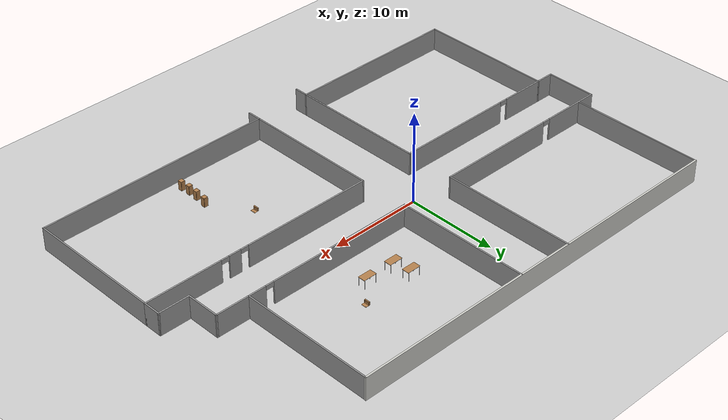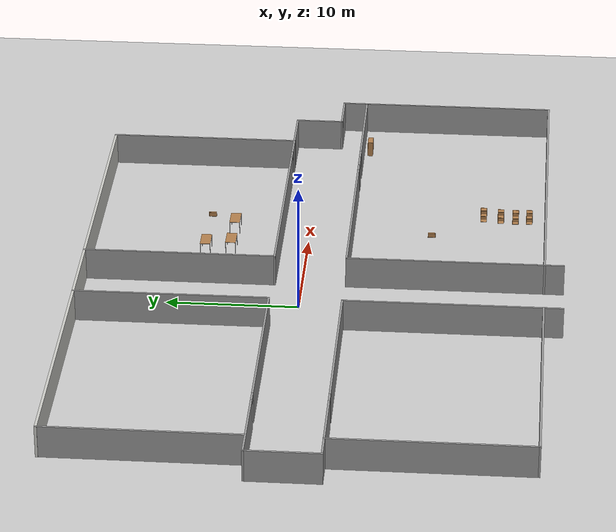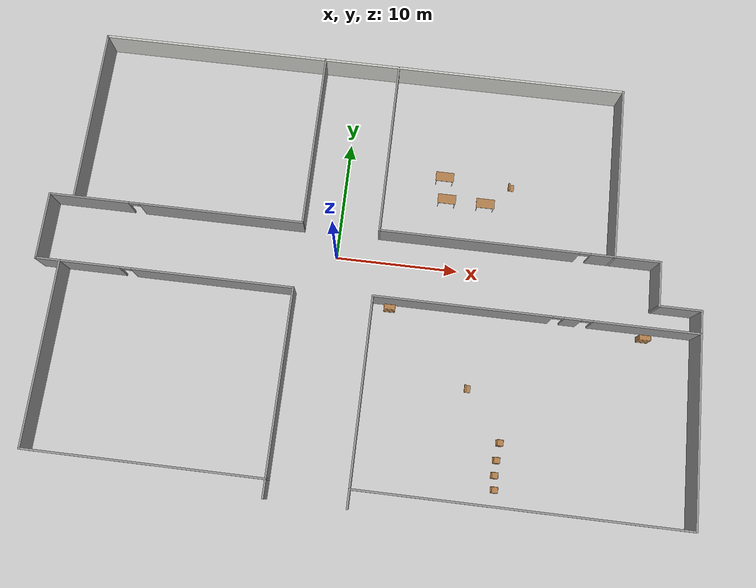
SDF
<sdf version="1.6">
 <world name="default">
  <light name="sun" type="directional">
   <pose>0 0 10 0 -0 0</pose>
   <diffuse>0.8 0.8 0.8 1</diffuse>
   <specular>0.2 0.2 0.2 1</specular>
   <attenuation>
    <range>1000</range>
    <constant>0.9</constant>
    <linear>0.01</linear>
    <quadratic>0.001</quadratic>
   </attenuation>
   <direction>-0.5 0.1 -0.9</direction>
  </light>
  <model name="ground_plane">
   <static>1</static>
   <link name="link">
    <collision name="collision">
     <geometry><plane><normal>0 0 1</normal><size>100 100</size></plane></geometry>
     <surface>
      <contact><collide_bitmask>65535</collide_bitmask></contact>
      <friction><ode><mu>100</mu><mu2>50</mu2></ode></friction>
     </surface>
    </collision>
    <visual name="visual">
     <cast_shadows>0</cast_shadows>
     <geometry><plane><normal>0 0 1</normal><size>100 100</size></plane></geometry>
     <material>
      <script><uri>file://media/materials/scripts/gazebo.material</uri><name>Gazebo/Grey</name></script>
     </material>
    </visual>
   </link>
  </model>
  <gravity>0 0 -9.8</gravity>
  <magnetic_field>6e-06 2.3e-05 -4.2e-05</magnetic_field>
  <atmosphere type="adiabatic"/>
  <physics name="default_physics" default="0" type="ode">
   <max_step_size>0.001</max_step_size>
   <real_time_factor>1</real_time_factor>
   <real_time_update_rate>1000</real_time_update_rate>
  </physics>
  <scene><ambient>0.4 0.4 0.4 1</ambient><background>0.7 0.7 0.7 1</background><shadows>1</shadows></scene>
  <audio><device>default</device></audio>
  <spherical_coordinates>
   <surface_model>EARTH_WGS84</surface_model>
   <latitude_deg>0</latitude_deg>
   <longitude_deg>0</longitude_deg>
   <elevation>0</elevation>
   <heading_deg>0</heading_deg>
  </spherical_coordinates>
  <model name="H_Block_Model">
   <link name="Wall_10">
    <pose>-26.5 0.832901 0 0 0 -1.5708</pose>
    <visual name="Wall_10_Visual">
     <pose>0 0 1.25 0 -0 0</pose>
     <geometry><box><size>5.593 0.15 2.5</size></box></geometry>
     <material>
      <script><uri>file://media/materials/scripts/gazebo.material</uri><name>Gazebo/Grey</name></script>
      <ambient>1 1 1 1</ambient>
     </material>
     <meta><layer>0</layer></meta>
    </visual>
    <collision name="Wall_10_Collision">
     <pose>0 0 1.25 0 -0 0</pose>
     <geometry><box><size>5.593 0.15 2.5</size></box></geometry>
     <surface>
      <friction>
       <ode><mu>1</mu><mu2>1</mu2><fdir1>0 0 0</fdir1><slip1>0</slip1><slip2>0</slip2></ode>
       <torsional>
        <coefficient>1</coefficient>
        <patch_radius>0</patch_radius>
        <surface_radius>0</surface_radius>
        <use_patch_radius>1</use_patch_radius>
        <ode><slip>0</slip></ode>
       </torsional>
      </friction>
      <bounce><restitution_coefficient>0</restitution_coefficient><threshold>1e+06</threshold></bounce>
      <contact>
       <collide_without_contact>0</collide_without_contact>
       <collide_without_contact_bitmask>1</collide_without_contact_bitmask>
       <collide_bitmask>1</collide_bitmask>
       <ode>
        <soft_cfm>0</soft_cfm>
        <soft_erp>0.2</soft_erp>
        <kp>1e+13</kp>
        <kd>1</kd>
        <max_vel>0.01</max_vel>
        <min_depth>0</min_depth>
       </ode>
       <bullet>
        <split_impulse>1</split_impulse>
        <split_impulse_penetration_threshold>-0.01</split_impulse_penetration_threshold>
        <soft_cfm>0</soft_cfm>
        <soft_erp>0.2</soft_erp>
        <kp>1e+13</kp>
        <kd>1</kd>
       </bullet>
      </contact>
     </surface>
    </collision>
   </link>
   <link name="Wall_11">
    <pose>-16.11 -1.8886 0 0 -0 0</pose>
    <visual name="Wall_11_Visual_0">
     <pose>-7.00772 0 1.25 0 -0 0</pose>
     <geometry><box><size>6.9143 0.15 2.5</size></box></geometry>
     <material>
      <script><uri>file://media/materials/scripts/gazebo.material</uri><name>Gazebo/Grey</name></script>
      <ambient>1 1 1 1</ambient>
     </material>
     <meta><layer>0</layer></meta>
    </visual>
    <visual name="Wall_11_Visual_1">
     <pose>3.90715 0 1.25 0 -0 0</pose>
     <geometry><box><size>13.1154 0.15 2.5</size></box></geometry>
     <material>
      <script><uri>file://media/materials/scripts/gazebo.material</uri><name>Gazebo/Grey</name></script>
      <ambient>1 1 1 1</ambient>
     </material>
     <meta><layer>0</layer></meta>
    </visual>
    <visual name="Wall_11_Visual_2">
     <pose>-3.10057 0 2.25 0 -0 0</pose>
     <geometry><box><size>0.9 0.15 0.5</size></box></geometry>
     <material>
      <script><uri>file://media/materials/scripts/gazebo.material</uri><name>Gazebo/Grey</name></script>
      <ambient>1 1 1 1</ambient>
     </material>
     <meta><layer>0</layer></meta>
    </visual>
    <collision name="Wall_11_Collision_0">
     <pose>-7.00772 0 1.25 0 -0 0</pose>
     <geometry><box><size>6.9143 0.15 2.5</size></box></geometry>
     <surface>
      <friction>
       <ode><mu>1</mu><mu2>1</mu2><fdir1>0 0 0</fdir1><slip1>0</slip1><slip2>0</slip2></ode>
       <torsional>
        <coefficient>1</coefficient>
        <patch_radius>0</patch_radius>
        <surface_radius>0</surface_radius>
        <use_patch_radius>1</use_patch_radius>
        <ode><slip>0</slip></ode>
       </torsional>
      </friction>
      <bounce><restitution_coefficient>0</restitution_coefficient><threshold>1e+06</threshold></bounce>
      <contact>
       <collide_without_contact>0</collide_without_contact>
       <collide_without_contact_bitmask>1</collide_without_contact_bitmask>
       <collide_bitmask>1</collide_bitmask>
       <ode>
        <soft_cfm>0</soft_cfm>
        <soft_erp>0.2</soft_erp>
        <kp>1e+13</kp>
        <kd>1</kd>
        <max_vel>0.01</max_vel>
        <min_depth>0</min_depth>
       </ode>
       <bullet>
        <split_impulse>1</split_impulse>
        <split_impulse_penetration_threshold>-0.01</split_impulse_penetration_threshold>
        <soft_cfm>0</soft_cfm>
        <soft_erp>0.2</soft_erp>
        <kp>1e+13</kp>
        <kd>1</kd>
       </bullet>
      </contact>
     </surface>
    </collision>
    <collision name="Wall_11_Collision_1">
     <pose>3.90715 0 1.25 0 -0 0</pose>
     <geometry><box><size>13.1154 0.15 2.5</size></box></geometry>
     <surface>
      <friction>
       <ode><mu>1</mu><mu2>1</mu2><fdir1>0 0 0</fdir1><slip1>0</slip1><slip2>0</slip2></ode>
       <torsional>
        <coefficient>1</coefficient>
        <patch_radius>0</patch_radius>
        <surface_radius>0</surface_radius>
        <use_patch_radius>1</use_patch_radius>
        <ode><slip>0</slip></ode>
       </torsional>
      </friction>
      <bounce><restitution_coefficient>0</restitution_coefficient><threshold>1e+06</threshold></bounce>
      <contact>
       <collide_without_contact>0</collide_without_contact>
       <collide_without_contact_bitmask>1</collide_without_contact_bitmask>
       <collide_bitmask>1</collide_bitmask>
       <ode>
        <soft_cfm>0</soft_cfm>
        <soft_erp>0.2</soft_erp>
        <kp>1e+13</kp>
        <kd>1</kd>
        <max_vel>0.01</max_vel>
        <min_depth>0</min_depth>
       </ode>
       <bullet>
        <split_impulse>1</split_impulse>
        <split_impulse_penetration_threshold>-0.01</split_impulse_penetration_threshold>
        <soft_cfm>0</soft_cfm>
        <soft_erp>0.2</soft_erp>
        <kp>1e+13</kp>
        <kd>1</kd>
       </bullet>
      </contact>
     </surface>
    </collision>
    <collision name="Wall_11_Collision_2">
     <pose>-3.10057 0 2.25 0 -0 0</pose>
     <geometry><box><size>0.9 0.15 0.5</size></box></geometry>
     <surface>
      <friction>
       <ode><mu>1</mu><mu2>1</mu2><fdir1>0 0 0</fdir1><slip1>0</slip1><slip2>0</slip2></ode>
       <torsional>
        <coefficient>1</coefficient>
        <patch_radius>0</patch_radius>
        <surface_radius>0</surface_radius>
        <use_patch_radius>1</use_patch_radius>
        <ode><slip>0</slip></ode>
       </torsional>
      </friction>
      <bounce><restitution_coefficient>0</restitution_coefficient><threshold>1e+06</threshold></bounce>
      <contact>
       <collide_without_contact>0</collide_without_contact>
       <collide_without_contact_bitmask>1</collide_without_contact_bitmask>
       <collide_bitmask>1</collide_bitmask>
       <ode>
        <soft_cfm>0</soft_cfm>
        <soft_erp>0.2</soft_erp>
        <kp>1e+13</kp>
        <kd>1</kd>
        <max_vel>0.01</max_vel>
        <min_depth>0</min_depth>
       </ode>
       <bullet>
        <split_impulse>1</split_impulse>
        <split_impulse_penetration_threshold>-0.01</split_impulse_penetration_threshold>
        <soft_cfm>0</soft_cfm>
        <soft_erp>0.2</soft_erp>
        <kp>1e+13</kp>
        <kd>1</kd>
       </bullet>
      </contact>
     </surface>
    </collision>
   </link>
   <link name="Wall_12">
    <pose>-5.72016 -10.0169 0 0 0 -1.57082</pose>
    <visual name="Wall_12_Visual">
     <pose>0 0 1.25 0 -0 0</pose>
     <geometry><box><size>16.407 0.15 2.5</size></box></geometry>
     <material>
      <script><uri>file://media/materials/scripts/gazebo.material</uri><name>Gazebo/Grey</name></script>
      <ambient>1 1 1 1</ambient>
     </material>
     <meta><layer>0</layer></meta>
    </visual>
    <collision name="Wall_12_Collision">
     <pose>0 0 1.25 0 -0 0</pose>
     <geometry><box><size>16.407 0.15 2.5</size></box></geometry>
     <surface>
      <friction>
       <ode><mu>1</mu><mu2>1</mu2><fdir1>0 0 0</fdir1><slip1>0</slip1><slip2>0</slip2></ode>
       <torsional>
        <coefficient>1</coefficient>
        <patch_radius>0</patch_radius>
        <surface_radius>0</surface_radius>
        <use_patch_radius>1</use_patch_radius>
        <ode><slip>0</slip></ode>
       </torsional>
      </friction>
      <bounce><restitution_coefficient>0</restitution_coefficient><threshold>1e+06</threshold></bounce>
      <contact>
       <collide_without_contact>0</collide_without_contact>
       <collide_without_contact_bitmask>1</collide_without_contact_bitmask>
       <collide_bitmask>1</collide_bitmask>
       <ode>
        <soft_cfm>0</soft_cfm>
        <soft_erp>0.2</soft_erp>
        <kp>1e+13</kp>
        <kd>1</kd>
        <max_vel>0.01</max_vel>
        <min_depth>0</min_depth>
       </ode>
       <bullet>
        <split_impulse>1</split_impulse>
        <split_impulse_penetration_threshold>-0.01</split_impulse_penetration_threshold>
        <soft_cfm>0</soft_cfm>
        <soft_erp>0.2</soft_erp>
        <kp>1e+13</kp>
        <kd>1</kd>
       </bullet>
      </contact>
     </surface>
    </collision>
   </link>
   <link name="Wall_14">
    <pose>0.629841 -9.9704 0 0 -0 1.57078</pose>
    <visual name="Wall_14_Visual">
     <pose>0 0 1.25 0 -0 0</pose>
     <geometry><box><size>16.5 0.15 2.5</size></box></geometry>
     <material>
      <script><uri>file://media/materials/scripts/gazebo.material</uri><name>Gazebo/Grey</name></script>
      <ambient>1 1 1 1</ambient>
     </material>
     <meta><layer>0</layer></meta>
    </visual>
    <collision name="Wall_14_Collision">
     <pose>0 0 1.25 0 -0 0</pose>
     <geometry><box><size>16.5 0.15 2.5</size></box></geometry>
     <surface>
      <friction>
       <ode><mu>1</mu><mu2>1</mu2><fdir1>0 0 0</fdir1><slip1>0</slip1><slip2>0</slip2></ode>
       <torsional>
        <coefficient>1</coefficient>
        <patch_radius>0</patch_radius>
        <surface_radius>0</surface_radius>
        <use_patch_radius>1</use_patch_radius>
        <ode><slip>0</slip></ode>
       </torsional>
      </friction>
      <bounce><restitution_coefficient>0</restitution_coefficient><threshold>1e+06</threshold></bounce>
      <contact>
       <collide_without_contact>0</collide_without_contact>
       <collide_without_contact_bitmask>1</collide_without_contact_bitmask>
       <collide_bitmask>1</collide_bitmask>
       <ode>
        <soft_cfm>0</soft_cfm>
        <soft_erp>0.2</soft_erp>
        <kp>1e+13</kp>
        <kd>1</kd>
        <max_vel>0.01</max_vel>
        <min_depth>0</min_depth>
       </ode>
       <bullet>
        <split_impulse>1</split_impulse>
        <split_impulse_penetration_threshold>-0.01</split_impulse_penetration_threshold>
        <soft_cfm>0</soft_cfm>
        <soft_erp>0.2</soft_erp>
        <kp>1e+13</kp>
        <kd>1</kd>
       </bullet>
      </contact>
     </surface>
    </collision>
   </link>
   <link name="Wall_15">
    <pose>13.565 -1.7956 0 0 -0 0</pose>
    <visual name="Wall_15_Visual_0">
     <pose>-5.84501 0 1.25 0 -0 0</pose>
     <geometry><box><size>14.33 0.15 2.5</size></box></geometry>
     <material>
      <script><uri>file://media/materials/scripts/gazebo.material</uri><name>Gazebo/Grey</name></script>
      <ambient>1 1 1 1</ambient>
     </material>
     <meta><layer>0</layer></meta>
    </visual>
    <visual name="Wall_15_Visual_1">
     <pose>2.89569 0 1.25 0 -0 0</pose>
     <geometry><box><size>1.35144 0.15 2.5</size></box></geometry>
     <material>
      <script><uri>file://media/materials/scripts/gazebo.material</uri><name>Gazebo/Grey</name></script>
      <ambient>1 1 1 1</ambient>
     </material>
     <meta><layer>0</layer></meta>
    </visual>
    <visual name="Wall_15_Visual_2">
     <pose>8.74071 0 1.25 0 -0 0</pose>
     <geometry><box><size>8.53858 0.15 2.5</size></box></geometry>
     <material>
      <script><uri>file://media/materials/scripts/gazebo.material</uri><name>Gazebo/Grey</name></script>
      <ambient>1 1 1 1</ambient>
     </material>
     <meta><layer>0</layer></meta>
    </visual>
    <visual name="Wall_15_Visual_3">
     <pose>1.76997 0 2.25 0 -0 0</pose>
     <geometry><box><size>0.9 0.15 0.5</size></box></geometry>
     <material>
      <script><uri>file://media/materials/scripts/gazebo.material</uri><name>Gazebo/Grey</name></script>
      <ambient>1 1 1 1</ambient>
     </material>
     <meta><layer>0</layer></meta>
    </visual>
    <visual name="Wall_15_Visual_4">
     <pose>4.02142 0 2.25 0 -0 0</pose>
     <geometry><box><size>0.9 0.15 0.5</size></box></geometry>
     <material>
      <script><uri>file://media/materials/scripts/gazebo.material</uri><name>Gazebo/Grey</name></script>
      <ambient>1 1 1 1</ambient>
     </material>
     <meta><layer>0</layer></meta>
    </visual>
    <collision name="Wall_15_Collision_0">
     <pose>-5.84501 0 1.25 0 -0 0</pose>
     <geometry><box><size>14.33 0.15 2.5</size></box></geometry>
     <surface>
      <friction>
       <ode><mu>1</mu><mu2>1</mu2><fdir1>0 0 0</fdir1><slip1>0</slip1><slip2>0</slip2></ode>
       <torsional>
        <coefficient>1</coefficient>
        <patch_radius>0</patch_radius>
        <surface_radius>0</surface_radius>
        <use_patch_radius>1</use_patch_radius>
        <ode><slip>0</slip></ode>
       </torsional>
      </friction>
      <bounce><restitution_coefficient>0</restitution_coefficient><threshold>1e+06</threshold></bounce>
      <contact>
       <collide_without_contact>0</collide_without_contact>
       <collide_without_contact_bitmask>1</collide_without_contact_bitmask>
       <collide_bitmask>1</collide_bitmask>
       <ode>
        <soft_cfm>0</soft_cfm>
        <soft_erp>0.2</soft_erp>
        <kp>1e+13</kp>
        <kd>1</kd>
        <max_vel>0.01</max_vel>
        <min_depth>0</min_depth>
       </ode>
       <bullet>
        <split_impulse>1</split_impulse>
        <split_impulse_penetration_threshold>-0.01</split_impulse_penetration_threshold>
        <soft_cfm>0</soft_cfm>
        <soft_erp>0.2</soft_erp>
        <kp>1e+13</kp>
        <kd>1</kd>
       </bullet>
      </contact>
     </surface>
    </collision>
    <collision name="Wall_15_Collision_1">
     <pose>2.89569 0 1.25 0 -0 0</pose>
     <geometry><box><size>1.35144 0.15 2.5</size></box></geometry>
     <surface>
      <friction>
       <ode><mu>1</mu><mu2>1</mu2><fdir1>0 0 0</fdir1><slip1>0</slip1><slip2>0</slip2></ode>
       <torsional>
        <coefficient>1</coefficient>
        <patch_radius>0</patch_radius>
        <surface_radius>0</surface_radius>
        <use_patch_radius>1</use_patch_radius>
        <ode><slip>0</slip></ode>
       </torsional>
      </friction>
      <bounce><restitution_coefficient>0</restitution_coefficient><threshold>1e+06</threshold></bounce>
      <contact>
       <collide_without_contact>0</collide_without_contact>
       <collide_without_contact_bitmask>1</collide_without_contact_bitmask>
       <collide_bitmask>1</collide_bitmask>
       <ode>
        <soft_cfm>0</soft_cfm>
        <soft_erp>0.2</soft_erp>
        <kp>1e+13</kp>
        <kd>1</kd>
        <max_vel>0.01</max_vel>
        <min_depth>0</min_depth>
       </ode>
       <bullet>
        <split_impulse>1</split_impulse>
        <split_impulse_penetration_threshold>-0.01</split_impulse_penetration_threshold>
        <soft_cfm>0</soft_cfm>
        <soft_erp>0.2</soft_erp>
        <kp>1e+13</kp>
        <kd>1</kd>
       </bullet>
      </contact>
     </surface>
    </collision>
    <collision name="Wall_15_Collision_2">
     <pose>8.74071 0 1.25 0 -0 0</pose>
     <geometry><box><size>8.53858 0.15 2.5</size></box></geometry>
     <surface>
      <friction>
       <ode><mu>1</mu><mu2>1</mu2><fdir1>0 0 0</fdir1><slip1>0</slip1><slip2>0</slip2></ode>
       <torsional>
        <coefficient>1</coefficient>
        <patch_radius>0</patch_radius>
        <surface_radius>0</surface_radius>
        <use_patch_radius>1</use_patch_radius>
        <ode><slip>0</slip></ode>
       </torsional>
      </friction>
      <bounce><restitution_coefficient>0</restitution_coefficient><threshold>1e+06</threshold></bounce>
      <contact>
       <collide_without_contact>0</collide_without_contact>
       <collide_without_contact_bitmask>1</collide_without_contact_bitmask>
       <collide_bitmask>1</collide_bitmask>
       <ode>
        <soft_cfm>0</soft_cfm>
        <soft_erp>0.2</soft_erp>
        <kp>1e+13</kp>
        <kd>1</kd>
        <max_vel>0.01</max_vel>
        <min_depth>0</min_depth>
       </ode>
       <bullet>
        <split_impulse>1</split_impulse>
        <split_impulse_penetration_threshold>-0.01</split_impulse_penetration_threshold>
        <soft_cfm>0</soft_cfm>
        <soft_erp>0.2</soft_erp>
        <kp>1e+13</kp>
        <kd>1</kd>
       </bullet>
      </contact>
     </surface>
    </collision>
    <collision name="Wall_15_Collision_3">
     <pose>1.76997 0 2.25 0 -0 0</pose>
     <geometry><box><size>0.9 0.15 0.5</size></box></geometry>
     <surface>
      <friction>
       <ode><mu>1</mu><mu2>1</mu2><fdir1>0 0 0</fdir1><slip1>0</slip1><slip2>0</slip2></ode>
       <torsional>
        <coefficient>1</coefficient>
        <patch_radius>0</patch_radius>
        <surface_radius>0</surface_radius>
        <use_patch_radius>1</use_patch_radius>
        <ode><slip>0</slip></ode>
       </torsional>
      </friction>
      <bounce><restitution_coefficient>0</restitution_coefficient><threshold>1e+06</threshold></bounce>
      <contact>
       <collide_without_contact>0</collide_without_contact>
       <collide_without_contact_bitmask>1</collide_without_contact_bitmask>
       <collide_bitmask>1</collide_bitmask>
       <ode>
        <soft_cfm>0</soft_cfm>
        <soft_erp>0.2</soft_erp>
        <kp>1e+13</kp>
        <kd>1</kd>
        <max_vel>0.01</max_vel>
        <min_depth>0</min_depth>
       </ode>
       <bullet>
        <split_impulse>1</split_impulse>
        <split_impulse_penetration_threshold>-0.01</split_impulse_penetration_threshold>
        <soft_cfm>0</soft_cfm>
        <soft_erp>0.2</soft_erp>
        <kp>1e+13</kp>
        <kd>1</kd>
       </bullet>
      </contact>
     </surface>
    </collision>
    <collision name="Wall_15_Collision_4">
     <pose>4.02142 0 2.25 0 -0 0</pose>
     <geometry><box><size>0.9 0.15 0.5</size></box></geometry>
     <surface>
      <friction>
       <ode><mu>1</mu><mu2>1</mu2><fdir1>0 0 0</fdir1><slip1>0</slip1><slip2>0</slip2></ode>
       <torsional>
        <coefficient>1</coefficient>
        <patch_radius>0</patch_radius>
        <surface_radius>0</surface_radius>
        <use_patch_radius>1</use_patch_radius>
        <ode><slip>0</slip></ode>
       </torsional>
      </friction>
      <bounce><restitution_coefficient>0</restitution_coefficient><threshold>1e+06</threshold></bounce>
      <contact>
       <collide_without_contact>0</collide_without_contact>
       <collide_without_contact_bitmask>1</collide_without_contact_bitmask>
       <collide_bitmask>1</collide_bitmask>
       <ode>
        <soft_cfm>0</soft_cfm>
        <soft_erp>0.2</soft_erp>
        <kp>1e+13</kp>
        <kd>1</kd>
        <max_vel>0.01</max_vel>
        <min_depth>0</min_depth>
       </ode>
       <bullet>
        <split_impulse>1</split_impulse>
        <split_impulse_penetration_threshold>-0.01</split_impulse_penetration_threshold>
        <soft_cfm>0</soft_cfm>
        <soft_erp>0.2</soft_erp>
        <kp>1e+13</kp>
        <kd>1</kd>
       </bullet>
      </contact>
     </surface>
    </collision>
   </link>
   <link name="Wall_2">
    <pose>-2.507 18.1204 0 0 -0 0</pose>
    <visual name="Wall_2_Visual">
     <pose>0 0 1.25 0 -0 0</pose>
     <geometry><box><size>44.214 0.2 2.5</size></box></geometry>
     <material>
      <script><uri>file://media/materials/scripts/gazebo.material</uri><name>Gazebo/CeilingTiled</name></script>
      <ambient>1 1 1 1</ambient>
     </material>
     <meta><layer>0</layer></meta>
    </visual>
    <collision name="Wall_2_Collision">
     <pose>0 0 1.25 0 -0 0</pose>
     <geometry><box><size>44.214 0.2 2.5</size></box></geometry>
     <surface>
      <friction>
       <ode><mu>1</mu><mu2>1</mu2><fdir1>0 0 0</fdir1><slip1>0</slip1><slip2>0</slip2></ode>
       <torsional>
        <coefficient>1</coefficient>
        <patch_radius>0</patch_radius>
        <surface_radius>0</surface_radius>
        <use_patch_radius>1</use_patch_radius>
        <ode><slip>0</slip></ode>
       </torsional>
      </friction>
      <bounce><restitution_coefficient>0</restitution_coefficient><threshold>1e+06</threshold></bounce>
      <contact>
       <collide_without_contact>0</collide_without_contact>
       <collide_without_contact_bitmask>1</collide_without_contact_bitmask>
       <collide_bitmask>1</collide_bitmask>
       <ode>
        <soft_cfm>0</soft_cfm>
        <soft_erp>0.2</soft_erp>
        <kp>1e+13</kp>
        <kd>1</kd>
        <max_vel>0.01</max_vel>
        <min_depth>0</min_depth>
       </ode>
       <bullet>
        <split_impulse>1</split_impulse>
        <split_impulse_penetration_threshold>-0.01</split_impulse_penetration_threshold>
        <soft_cfm>0</soft_cfm>
        <soft_erp>0.2</soft_erp>
        <kp>1e+13</kp>
        <kd>1</kd>
       </bullet>
      </contact>
     </surface>
    </collision>
   </link>
   <link name="Wall_20">
    <pose>0.53 10.8874 0 0 -0 1.5708</pose>
    <visual name="Wall_20_Visual">
     <pose>0 0 1.25 0 -0 0</pose>
     <geometry><box><size>14.616 0.15 2.5</size></box></geometry>
     <material>
      <script><uri>file://media/materials/scripts/gazebo.material</uri><name>Gazebo/Grey</name></script>
      <ambient>1 1 1 1</ambient>
     </material>
     <meta><layer>0</layer></meta>
    </visual>
    <collision name="Wall_20_Collision">
     <pose>0 0 1.25 0 -0 0</pose>
     <geometry><box><size>14.616 0.15 2.5</size></box></geometry>
     <surface>
      <friction>
       <ode><mu>1</mu><mu2>1</mu2><fdir1>0 0 0</fdir1><slip1>0</slip1><slip2>0</slip2></ode>
       <torsional>
        <coefficient>1</coefficient>
        <patch_radius>0</patch_radius>
        <surface_radius>0</surface_radius>
        <use_patch_radius>1</use_patch_radius>
        <ode><slip>0</slip></ode>
       </torsional>
      </friction>
      <bounce><restitution_coefficient>0</restitution_coefficient><threshold>1e+06</threshold></bounce>
      <contact>
       <collide_without_contact>0</collide_without_contact>
       <collide_without_contact_bitmask>1</collide_without_contact_bitmask>
       <collide_bitmask>1</collide_bitmask>
       <ode>
        <soft_cfm>0</soft_cfm>
        <soft_erp>0.2</soft_erp>
        <kp>1e+13</kp>
        <kd>1</kd>
        <max_vel>0.01</max_vel>
        <min_depth>0</min_depth>
       </ode>
       <bullet>
        <split_impulse>1</split_impulse>
        <split_impulse_penetration_threshold>-0.01</split_impulse_penetration_threshold>
        <soft_cfm>0</soft_cfm>
        <soft_erp>0.2</soft_erp>
        <kp>1e+13</kp>
        <kd>1</kd>
       </bullet>
      </contact>
     </surface>
    </collision>
   </link>
   <link name="Wall_22">
    <pose>26.5 -0.870599 0 0 -0 1.5708</pose>
    <visual name="Wall_22_Visual">
     <pose>0 0 1.25 0 -0 0</pose>
     <geometry><box><size>2 0.15 2.5</size></box></geometry>
     <material>
      <script><uri>file://media/materials/scripts/gazebo.material</uri><name>Gazebo/Grey</name></script>
      <ambient>1 1 1 1</ambient>
     </material>
     <meta><layer>0</layer></meta>
    </visual>
    <collision name="Wall_22_Collision">
     <pose>0 0 1.25 0 -0 0</pose>
     <geometry><box><size>2 0.15 2.5</size></box></geometry>
     <surface>
      <friction>
       <ode><mu>1</mu><mu2>1</mu2><fdir1>0 0 0</fdir1><slip1>0</slip1><slip2>0</slip2></ode>
       <torsional>
        <coefficient>1</coefficient>
        <patch_radius>0</patch_radius>
        <surface_radius>0</surface_radius>
        <use_patch_radius>1</use_patch_radius>
        <ode><slip>0</slip></ode>
       </torsional>
      </friction>
      <bounce><restitution_coefficient>0</restitution_coefficient><threshold>1e+06</threshold></bounce>
      <contact>
       <collide_without_contact>0</collide_without_contact>
       <collide_without_contact_bitmask>1</collide_without_contact_bitmask>
       <collide_bitmask>1</collide_bitmask>
       <ode>
        <soft_cfm>0</soft_cfm>
        <soft_erp>0.2</soft_erp>
        <kp>1e+13</kp>
        <kd>1</kd>
        <max_vel>0.01</max_vel>
        <min_depth>0</min_depth>
       </ode>
       <bullet>
        <split_impulse>1</split_impulse>
        <split_impulse_penetration_threshold>-0.01</split_impulse_penetration_threshold>
        <soft_cfm>0</soft_cfm>
        <soft_erp>0.2</soft_erp>
        <kp>1e+13</kp>
        <kd>1</kd>
       </bullet>
      </contact>
     </surface>
    </collision>
   </link>
   <link name="Wall_23">
    <pose>24.825 0.054401 0 0 -0 3.14159</pose>
    <visual name="Wall_23_Visual">
     <pose>0 0 1.25 0 -0 0</pose>
     <geometry><box><size>3.5 0.15 2.5</size></box></geometry>
     <material>
      <script><uri>file://media/materials/scripts/gazebo.material</uri><name>Gazebo/Grey</name></script>
      <ambient>1 1 1 1</ambient>
     </material>
     <meta><layer>0</layer></meta>
    </visual>
    <collision name="Wall_23_Collision">
     <pose>0 0 1.25 0 -0 0</pose>
     <geometry><box><size>3.5 0.15 2.5</size></box></geometry>
     <surface>
      <friction>
       <ode><mu>1</mu><mu2>1</mu2><fdir1>0 0 0</fdir1><slip1>0</slip1><slip2>0</slip2></ode>
       <torsional>
        <coefficient>1</coefficient>
        <patch_radius>0</patch_radius>
        <surface_radius>0</surface_radius>
        <use_patch_radius>1</use_patch_radius>
        <ode><slip>0</slip></ode>
       </torsional>
      </friction>
      <bounce><restitution_coefficient>0</restitution_coefficient><threshold>1e+06</threshold></bounce>
      <contact>
       <collide_without_contact>0</collide_without_contact>
       <collide_without_contact_bitmask>1</collide_without_contact_bitmask>
       <collide_bitmask>1</collide_bitmask>
       <ode>
        <soft_cfm>0</soft_cfm>
        <soft_erp>0.2</soft_erp>
        <kp>1e+13</kp>
        <kd>1</kd>
        <max_vel>0.01</max_vel>
        <min_depth>0</min_depth>
       </ode>
       <bullet>
        <split_impulse>1</split_impulse>
        <split_impulse_penetration_threshold>-0.01</split_impulse_penetration_threshold>
        <soft_cfm>0</soft_cfm>
        <soft_erp>0.2</soft_erp>
        <kp>1e+13</kp>
        <kd>1</kd>
       </bullet>
      </contact>
     </surface>
    </collision>
   </link>
   <link name="Wall_24">
    <pose>23.15 1.8544 0 0 -0 1.5708</pose>
    <visual name="Wall_24_Visual">
     <pose>0 0 1.25 0 -0 0</pose>
     <geometry><box><size>3.75 0.15 2.5</size></box></geometry>
     <material>
      <script><uri>file://media/materials/scripts/gazebo.material</uri><name>Gazebo/Grey</name></script>
      <ambient>1 1 1 1</ambient>
     </material>
     <meta><layer>0</layer></meta>
    </visual>
    <collision name="Wall_24_Collision">
     <pose>0 0 1.25 0 -0 0</pose>
     <geometry><box><size>3.75 0.15 2.5</size></box></geometry>
     <surface>
      <friction>
       <ode><mu>1</mu><mu2>1</mu2><fdir1>0 0 0</fdir1><slip1>0</slip1><slip2>0</slip2></ode>
       <torsional>
        <coefficient>1</coefficient>
        <patch_radius>0</patch_radius>
        <surface_radius>0</surface_radius>
        <use_patch_radius>1</use_patch_radius>
        <ode><slip>0</slip></ode>
       </torsional>
      </friction>
      <bounce><restitution_coefficient>0</restitution_coefficient><threshold>1e+06</threshold></bounce>
      <contact>
       <collide_without_contact>0</collide_without_contact>
       <collide_without_contact_bitmask>1</collide_without_contact_bitmask>
       <collide_bitmask>1</collide_bitmask>
       <ode>
        <soft_cfm>0</soft_cfm>
        <soft_erp>0.2</soft_erp>
        <kp>1e+13</kp>
        <kd>1</kd>
        <max_vel>0.01</max_vel>
        <min_depth>0</min_depth>
       </ode>
       <bullet>
        <split_impulse>1</split_impulse>
        <split_impulse_penetration_threshold>-0.01</split_impulse_penetration_threshold>
        <soft_cfm>0</soft_cfm>
        <soft_erp>0.2</soft_erp>
        <kp>1e+13</kp>
        <kd>1</kd>
       </bullet>
      </contact>
     </surface>
    </collision>
   </link>
   <link name="Wall_25">
    <pose>11.84 3.6544 0 0 -0 3.14159</pose>
    <visual name="Wall_25_Visual_0">
     <pose>-8.56212 0 1.25 0 -0 0</pose>
     <geometry><box><size>5.64607 0.15 2.5</size></box></geometry>
     <material>
      <script><uri>file://media/materials/scripts/gazebo.material</uri><name>Gazebo/Grey</name></script>
      <ambient>1 1 1 1</ambient>
     </material>
     <meta><layer>0</layer></meta>
    </visual>
    <visual name="Wall_25_Visual_1">
     <pose>3.27303 0 1.25 0 -0 0</pose>
     <geometry><box><size>16.2242 0.15 2.5</size></box></geometry>
     <material>
      <script><uri>file://media/materials/scripts/gazebo.material</uri><name>Gazebo/Grey</name></script>
      <ambient>1 1 1 1</ambient>
     </material>
     <meta><layer>0</layer></meta>
    </visual>
    <visual name="Wall_25_Visual_2">
     <pose>-5.28909 0 2.25 0 -0 0</pose>
     <geometry><box><size>0.9 0.15 0.5</size></box></geometry>
     <material>
      <script><uri>file://media/materials/scripts/gazebo.material</uri><name>Gazebo/Grey</name></script>
      <ambient>1 1 1 1</ambient>
     </material>
     <meta><layer>0</layer></meta>
    </visual>
    <collision name="Wall_25_Collision_0">
     <pose>-8.56212 0 1.25 0 -0 0</pose>
     <geometry><box><size>5.64607 0.15 2.5</size></box></geometry>
     <surface>
      <friction>
       <ode><mu>1</mu><mu2>1</mu2><fdir1>0 0 0</fdir1><slip1>0</slip1><slip2>0</slip2></ode>
       <torsional>
        <coefficient>1</coefficient>
        <patch_radius>0</patch_radius>
        <surface_radius>0</surface_radius>
        <use_patch_radius>1</use_patch_radius>
        <ode><slip>0</slip></ode>
       </torsional>
      </friction>
      <bounce><restitution_coefficient>0</restitution_coefficient><threshold>1e+06</threshold></bounce>
      <contact>
       <collide_without_contact>0</collide_without_contact>
       <collide_without_contact_bitmask>1</collide_without_contact_bitmask>
       <collide_bitmask>1</collide_bitmask>
       <ode>
        <soft_cfm>0</soft_cfm>
        <soft_erp>0.2</soft_erp>
        <kp>1e+13</kp>
        <kd>1</kd>
        <max_vel>0.01</max_vel>
        <min_depth>0</min_depth>
       </ode>
       <bullet>
        <split_impulse>1</split_impulse>
        <split_impulse_penetration_threshold>-0.01</split_impulse_penetration_threshold>
        <soft_cfm>0</soft_cfm>
        <soft_erp>0.2</soft_erp>
        <kp>1e+13</kp>
        <kd>1</kd>
       </bullet>
      </contact>
     </surface>
    </collision>
    <collision name="Wall_25_Collision_1">
     <pose>3.27303 0 1.25 0 -0 0</pose>
     <geometry><box><size>16.2242 0.15 2.5</size></box></geometry>
     <surface>
      <friction>
       <ode><mu>1</mu><mu2>1</mu2><fdir1>0 0 0</fdir1><slip1>0</slip1><slip2>0</slip2></ode>
       <torsional>
        <coefficient>1</coefficient>
        <patch_radius>0</patch_radius>
        <surface_radius>0</surface_radius>
        <use_patch_radius>1</use_patch_radius>
        <ode><slip>0</slip></ode>
       </torsional>
      </friction>
      <bounce><restitution_coefficient>0</restitution_coefficient><threshold>1e+06</threshold></bounce>
      <contact>
       <collide_without_contact>0</collide_without_contact>
       <collide_without_contact_bitmask>1</collide_without_contact_bitmask>
       <collide_bitmask>1</collide_bitmask>
       <ode>
        <soft_cfm>0</soft_cfm>
        <soft_erp>0.2</soft_erp>
        <kp>1e+13</kp>
        <kd>1</kd>
        <max_vel>0.01</max_vel>
        <min_depth>0</min_depth>
       </ode>
       <bullet>
        <split_impulse>1</split_impulse>
        <split_impulse_penetration_threshold>-0.01</split_impulse_penetration_threshold>
        <soft_cfm>0</soft_cfm>
        <soft_erp>0.2</soft_erp>
        <kp>1e+13</kp>
        <kd>1</kd>
       </bullet>
      </contact>
     </surface>
    </collision>
    <collision name="Wall_25_Collision_2">
     <pose>-5.28909 0 2.25 0 -0 0</pose>
     <geometry><box><size>0.9 0.15 0.5</size></box></geometry>
     <surface>
      <friction>
       <ode><mu>1</mu><mu2>1</mu2><fdir1>0 0 0</fdir1><slip1>0</slip1><slip2>0</slip2></ode>
       <torsional>
        <coefficient>1</coefficient>
        <patch_radius>0</patch_radius>
        <surface_radius>0</surface_radius>
        <use_patch_radius>1</use_patch_radius>
        <ode><slip>0</slip></ode>
       </torsional>
      </friction>
      <bounce><restitution_coefficient>0</restitution_coefficient><threshold>1e+06</threshold></bounce>
      <contact>
       <collide_without_contact>0</collide_without_contact>
       <collide_without_contact_bitmask>1</collide_without_contact_bitmask>
       <collide_bitmask>1</collide_bitmask>
       <ode>
        <soft_cfm>0</soft_cfm>
        <soft_erp>0.2</soft_erp>
        <kp>1e+13</kp>
        <kd>1</kd>
        <max_vel>0.01</max_vel>
        <min_depth>0</min_depth>
       </ode>
       <bullet>
        <split_impulse>1</split_impulse>
        <split_impulse_penetration_threshold>-0.01</split_impulse_penetration_threshold>
        <soft_cfm>0</soft_cfm>
        <soft_erp>0.2</soft_erp>
        <kp>1e+13</kp>
        <kd>1</kd>
       </bullet>
      </contact>
     </surface>
    </collision>
   </link>
   <link name="Wall_27">
    <pose>-24.5588 -9.30178 0 0 0 -1.57082</pose>
    <visual name="Wall_27_Visual">
     <pose>0 0 1.25 0 -0 0</pose>
     <geometry><box><size>15 0.15 2.5</size></box></geometry>
     <material>
      <script><uri>file://media/materials/scripts/gazebo.material</uri><name>Gazebo/Grey</name></script>
      <ambient>1 1 1 1</ambient>
     </material>
     <meta><layer>0</layer></meta>
    </visual>
    <collision name="Wall_27_Collision">
     <pose>0 0 1.25 0 -0 0</pose>
     <geometry><box><size>15 0.15 2.5</size></box></geometry>
     <surface>
      <friction>
       <ode><mu>1</mu><mu2>1</mu2><fdir1>0 0 0</fdir1><slip1>0</slip1><slip2>0</slip2></ode>
       <torsional>
        <coefficient>1</coefficient>
        <patch_radius>0</patch_radius>
        <surface_radius>0</surface_radius>
        <use_patch_radius>1</use_patch_radius>
        <ode><slip>0</slip></ode>
       </torsional>
      </friction>
      <bounce><restitution_coefficient>0</restitution_coefficient><threshold>1e+06</threshold></bounce>
      <contact>
       <collide_without_contact>0</collide_without_contact>
       <collide_without_contact_bitmask>1</collide_without_contact_bitmask>
       <collide_bitmask>1</collide_bitmask>
       <ode>
        <soft_cfm>0</soft_cfm>
        <soft_erp>0.2</soft_erp>
        <kp>1e+13</kp>
        <kd>1</kd>
        <max_vel>0.01</max_vel>
        <min_depth>0</min_depth>
       </ode>
       <bullet>
        <split_impulse>1</split_impulse>
        <split_impulse_penetration_threshold>-0.01</split_impulse_penetration_threshold>
        <soft_cfm>0</soft_cfm>
        <soft_erp>0.2</soft_erp>
        <kp>1e+13</kp>
        <kd>1</kd>
       </bullet>
      </contact>
     </surface>
    </collision>
   </link>
   <link name="Wall_28">
    <pose>-15.1395 -16.7266 0 0 -0 0</pose>
    <visual name="Wall_28_Visual">
     <pose>0 0 1.25 0 -0 0</pose>
     <geometry><box><size>18.989 0.15 2.5</size></box></geometry>
     <material>
      <script><uri>file://media/materials/scripts/gazebo.material</uri><name>Gazebo/Grey</name></script>
      <ambient>1 1 1 1</ambient>
     </material>
     <meta><layer>0</layer></meta>
    </visual>
    <collision name="Wall_28_Collision">
     <pose>0 0 1.25 0 -0 0</pose>
     <geometry><box><size>18.989 0.15 2.5</size></box></geometry>
     <surface>
      <friction>
       <ode><mu>1</mu><mu2>1</mu2><fdir1>0 0 0</fdir1><slip1>0</slip1><slip2>0</slip2></ode>
       <torsional>
        <coefficient>1</coefficient>
        <patch_radius>0</patch_radius>
        <surface_radius>0</surface_radius>
        <use_patch_radius>1</use_patch_radius>
        <ode><slip>0</slip></ode>
       </torsional>
      </friction>
      <bounce><restitution_coefficient>0</restitution_coefficient><threshold>1e+06</threshold></bounce>
      <contact>
       <collide_without_contact>0</collide_without_contact>
       <collide_without_contact_bitmask>1</collide_without_contact_bitmask>
       <collide_bitmask>1</collide_bitmask>
       <ode>
        <soft_cfm>0</soft_cfm>
        <soft_erp>0.2</soft_erp>
        <kp>1e+13</kp>
        <kd>1</kd>
        <max_vel>0.01</max_vel>
        <min_depth>0</min_depth>
       </ode>
       <bullet>
        <split_impulse>1</split_impulse>
        <split_impulse_penetration_threshold>-0.01</split_impulse_penetration_threshold>
        <soft_cfm>0</soft_cfm>
        <soft_erp>0.2</soft_erp>
        <kp>1e+13</kp>
        <kd>1</kd>
       </bullet>
      </contact>
     </surface>
    </collision>
   </link>
   <link name="Wall_30">
    <pose>13.556 -16.7266 0 0 -0 0</pose>
    <visual name="Wall_30_Visual">
     <pose>0 0 1.25 0 -0 0</pose>
     <geometry><box><size>26.0375 0.15 2.5</size></box></geometry>
     <material>
      <script><uri>file://media/materials/scripts/gazebo.material</uri><name>Gazebo/Grey</name></script>
      <ambient>1 1 1 1</ambient>
     </material>
     <meta><layer>0</layer></meta>
    </visual>
    <collision name="Wall_30_Collision">
     <pose>0 0 1.25 0 -0 0</pose>
     <geometry><box><size>26.0375 0.15 2.5</size></box></geometry>
     <surface>
      <friction>
       <ode><mu>1</mu><mu2>1</mu2><fdir1>0 0 0</fdir1><slip1>0</slip1><slip2>0</slip2></ode>
       <torsional>
        <coefficient>1</coefficient>
        <patch_radius>0</patch_radius>
        <surface_radius>0</surface_radius>
        <use_patch_radius>1</use_patch_radius>
        <ode><slip>0</slip></ode>
       </torsional>
      </friction>
      <bounce><restitution_coefficient>0</restitution_coefficient><threshold>1e+06</threshold></bounce>
      <contact>
       <collide_without_contact>0</collide_without_contact>
       <collide_without_contact_bitmask>1</collide_without_contact_bitmask>
       <collide_bitmask>1</collide_bitmask>
       <ode>
        <soft_cfm>0</soft_cfm>
        <soft_erp>0.2</soft_erp>
        <kp>1e+13</kp>
        <kd>1</kd>
        <max_vel>0.01</max_vel>
        <min_depth>0</min_depth>
       </ode>
       <bullet>
        <split_impulse>1</split_impulse>
        <split_impulse_penetration_threshold>-0.01</split_impulse_penetration_threshold>
        <soft_cfm>0</soft_cfm>
        <soft_erp>0.2</soft_erp>
        <kp>1e+13</kp>
        <kd>1</kd>
       </bullet>
      </contact>
     </surface>
    </collision>
   </link>
   <link name="Wall_31">
    <pose>26.5 -9.2611 0 0 -0 1.5708</pose>
    <visual name="Wall_31_Visual">
     <pose>0 0 1.25 0 -0 0</pose>
     <geometry><box><size>15.081 0.15 2.5</size></box></geometry>
     <material>
      <script><uri>file://media/materials/scripts/gazebo.material</uri><name>Gazebo/Grey</name></script>
      <ambient>1 1 1 1</ambient>
     </material>
     <meta><layer>0</layer></meta>
    </visual>
    <collision name="Wall_31_Collision">
     <pose>0 0 1.25 0 -0 0</pose>
     <geometry><box><size>15.081 0.15 2.5</size></box></geometry>
     <surface>
      <friction>
       <ode><mu>1</mu><mu2>1</mu2><fdir1>0 0 0</fdir1><slip1>0</slip1><slip2>0</slip2></ode>
       <torsional>
        <coefficient>1</coefficient>
        <patch_radius>0</patch_radius>
        <surface_radius>0</surface_radius>
        <use_patch_radius>1</use_patch_radius>
        <ode><slip>0</slip></ode>
       </torsional>
      </friction>
      <bounce><restitution_coefficient>0</restitution_coefficient><threshold>1e+06</threshold></bounce>
      <contact>
       <collide_without_contact>0</collide_without_contact>
       <collide_without_contact_bitmask>1</collide_without_contact_bitmask>
       <collide_bitmask>1</collide_bitmask>
       <ode>
        <soft_cfm>0</soft_cfm>
        <soft_erp>0.2</soft_erp>
        <kp>1e+13</kp>
        <kd>1</kd>
        <max_vel>0.01</max_vel>
        <min_depth>0</min_depth>
       </ode>
       <bullet>
        <split_impulse>1</split_impulse>
        <split_impulse_penetration_threshold>-0.01</split_impulse_penetration_threshold>
        <soft_cfm>0</soft_cfm>
        <soft_erp>0.2</soft_erp>
        <kp>1e+13</kp>
        <kd>1</kd>
       </bullet>
      </contact>
     </surface>
    </collision>
   </link>
   <link name="Wall_4">
    <pose>-24.514 10.8869 0 0 0 -1.5708</pose>
    <visual name="Wall_4_Visual">
     <pose>0 0 1.25 0 -0 0</pose>
     <geometry><box><size>14.6174 0.15 2.5</size></box></geometry>
     <material>
      <script><uri>file://media/materials/scripts/gazebo.material</uri><name>Gazebo/Grey</name></script>
      <ambient>1 1 1 1</ambient>
     </material>
     <meta><layer>0</layer></meta>
    </visual>
    <collision name="Wall_4_Collision">
     <pose>0 0 1.25 0 -0 0</pose>
     <geometry><box><size>14.6174 0.15 2.5</size></box></geometry>
     <surface>
      <friction>
       <ode><mu>1</mu><mu2>1</mu2><fdir1>0 0 0</fdir1><slip1>0</slip1><slip2>0</slip2></ode>
       <torsional>
        <coefficient>1</coefficient>
        <patch_radius>0</patch_radius>
        <surface_radius>0</surface_radius>
        <use_patch_radius>1</use_patch_radius>
        <ode><slip>0</slip></ode>
       </torsional>
      </friction>
      <bounce><restitution_coefficient>0</restitution_coefficient><threshold>1e+06</threshold></bounce>
      <contact>
       <collide_without_contact>0</collide_without_contact>
       <collide_without_contact_bitmask>1</collide_without_contact_bitmask>
       <collide_bitmask>1</collide_bitmask>
       <ode>
        <soft_cfm>0</soft_cfm>
        <soft_erp>0.2</soft_erp>
        <kp>1e+13</kp>
        <kd>1</kd>
        <max_vel>0.01</max_vel>
        <min_depth>0</min_depth>
       </ode>
       <bullet>
        <split_impulse>1</split_impulse>
        <split_impulse_penetration_threshold>-0.01</split_impulse_penetration_threshold>
        <soft_cfm>0</soft_cfm>
        <soft_erp>0.2</soft_erp>
        <kp>1e+13</kp>
        <kd>1</kd>
       </bullet>
      </contact>
     </surface>
    </collision>
   </link>
   <link name="Wall_6">
    <pose>19.5 10.8869 0 0 0 -1.5708</pose>
    <visual name="Wall_6_Visual">
     <pose>0 0 1.25 0 -0 0</pose>
     <geometry><box><size>14.6174 0.15 2.5</size></box></geometry>
     <material>
      <script><uri>file://media/materials/scripts/gazebo.material</uri><name>Gazebo/Grey</name></script>
      <ambient>1 1 1 1</ambient>
     </material>
     <meta><layer>0</layer></meta>
    </visual>
    <collision name="Wall_6_Collision">
     <pose>0 0 1.25 0 -0 0</pose>
     <geometry><box><size>14.6174 0.15 2.5</size></box></geometry>
     <surface>
      <friction>
       <ode><mu>1</mu><mu2>1</mu2><fdir1>0 0 0</fdir1><slip1>0</slip1><slip2>0</slip2></ode>
       <torsional>
        <coefficient>1</coefficient>
        <patch_radius>0</patch_radius>
        <surface_radius>0</surface_radius>
        <use_patch_radius>1</use_patch_radius>
        <ode><slip>0</slip></ode>
       </torsional>
      </friction>
      <bounce><restitution_coefficient>0</restitution_coefficient><threshold>1e+06</threshold></bounce>
      <contact>
       <collide_without_contact>0</collide_without_contact>
       <collide_without_contact_bitmask>1</collide_without_contact_bitmask>
       <collide_bitmask>1</collide_bitmask>
       <ode>
        <soft_cfm>0</soft_cfm>
        <soft_erp>0.2</soft_erp>
        <kp>1e+13</kp>
        <kd>1</kd>
        <max_vel>0.01</max_vel>
        <min_depth>0</min_depth>
       </ode>
       <bullet>
        <split_impulse>1</split_impulse>
        <split_impulse_penetration_threshold>-0.01</split_impulse_penetration_threshold>
        <soft_cfm>0</soft_cfm>
        <soft_erp>0.2</soft_erp>
        <kp>1e+13</kp>
        <kd>1</kd>
       </bullet>
      </contact>
     </surface>
    </collision>
   </link>
   <link name="Wall_8">
    <pose>-5.72 10.8374 0 0 0 -1.5708</pose>
    <visual name="Wall_8_Visual">
     <pose>0 0 1.25 0 -0 0</pose>
     <geometry><box><size>14.716 0.15 2.5</size></box></geometry>
     <material>
      <script><uri>file://media/materials/scripts/gazebo.material</uri><name>Gazebo/Grey</name></script>
      <ambient>1 1 1 1</ambient>
     </material>
     <meta><layer>0</layer></meta>
    </visual>
    <collision name="Wall_8_Collision">
     <pose>0 0 1.25 0 -0 0</pose>
     <geometry><box><size>14.716 0.15 2.5</size></box></geometry>
     <surface>
      <friction>
       <ode><mu>1</mu><mu2>1</mu2><fdir1>0 0 0</fdir1><slip1>0</slip1><slip2>0</slip2></ode>
       <torsional>
        <coefficient>1</coefficient>
        <patch_radius>0</patch_radius>
        <surface_radius>0</surface_radius>
        <use_patch_radius>1</use_patch_radius>
        <ode><slip>0</slip></ode>
       </torsional>
      </friction>
      <bounce><restitution_coefficient>0</restitution_coefficient><threshold>1e+06</threshold></bounce>
      <contact>
       <collide_without_contact>0</collide_without_contact>
       <collide_without_contact_bitmask>1</collide_without_contact_bitmask>
       <collide_bitmask>1</collide_bitmask>
       <ode>
        <soft_cfm>0</soft_cfm>
        <soft_erp>0.2</soft_erp>
        <kp>1e+13</kp>
        <kd>1</kd>
        <max_vel>0.01</max_vel>
        <min_depth>0</min_depth>
       </ode>
       <bullet>
        <split_impulse>1</split_impulse>
        <split_impulse_penetration_threshold>-0.01</split_impulse_penetration_threshold>
        <soft_cfm>0</soft_cfm>
        <soft_erp>0.2</soft_erp>
        <kp>1e+13</kp>
        <kd>1</kd>
       </bullet>
      </contact>
     </surface>
    </collision>
   </link>
   <link name="Wall_9">
    <pose>-16.11 3.5544 0 0 -0 3.14159</pose>
    <visual name="Wall_9_Visual_0">
     <pose>-3.74891 0 1.25 0 -0 0</pose>
     <geometry><box><size>13.4322 0.15 2.5</size></box></geometry>
     <material>
      <script><uri>file://media/materials/scripts/gazebo.material</uri><name>Gazebo/Grey</name></script>
      <ambient>1 1 1 1</ambient>
     </material>
     <meta><layer>0</layer></meta>
    </visual>
    <visual name="Wall_9_Visual_1">
     <pose>7.16609 0 1.25 0 -0 0</pose>
     <geometry><box><size>6.59782 0.15 2.5</size></box></geometry>
     <material>
      <script><uri>file://media/materials/scripts/gazebo.material</uri><name>Gazebo/Grey</name></script>
      <ambient>1 1 1 1</ambient>
     </material>
     <meta><layer>0</layer></meta>
    </visual>
    <visual name="Wall_9_Visual_2">
     <pose>3.41718 0 2.25 0 -0 0</pose>
     <geometry><box><size>0.9 0.15 0.5</size></box></geometry>
     <material>
      <script><uri>file://media/materials/scripts/gazebo.material</uri><name>Gazebo/Grey</name></script>
      <ambient>1 1 1 1</ambient>
     </material>
     <meta><layer>0</layer></meta>
    </visual>
    <collision name="Wall_9_Collision_0">
     <pose>-3.74891 0 1.25 0 -0 0</pose>
     <geometry><box><size>13.4322 0.15 2.5</size></box></geometry>
     <surface>
      <friction>
       <ode><mu>1</mu><mu2>1</mu2><fdir1>0 0 0</fdir1><slip1>0</slip1><slip2>0</slip2></ode>
       <torsional>
        <coefficient>1</coefficient>
        <patch_radius>0</patch_radius>
        <surface_radius>0</surface_radius>
        <use_patch_radius>1</use_patch_radius>
        <ode><slip>0</slip></ode>
       </torsional>
      </friction>
      <bounce><restitution_coefficient>0</restitution_coefficient><threshold>1e+06</threshold></bounce>
      <contact>
       <collide_without_contact>0</collide_without_contact>
       <collide_without_contact_bitmask>1</collide_without_contact_bitmask>
       <collide_bitmask>1</collide_bitmask>
       <ode>
        <soft_cfm>0</soft_cfm>
        <soft_erp>0.2</soft_erp>
        <kp>1e+13</kp>
        <kd>1</kd>
        <max_vel>0.01</max_vel>
        <min_depth>0</min_depth>
       </ode>
       <bullet>
        <split_impulse>1</split_impulse>
        <split_impulse_penetration_threshold>-0.01</split_impulse_penetration_threshold>
        <soft_cfm>0</soft_cfm>
        <soft_erp>0.2</soft_erp>
        <kp>1e+13</kp>
        <kd>1</kd>
       </bullet>
      </contact>
     </surface>
    </collision>
    <collision name="Wall_9_Collision_1">
     <pose>7.16609 0 1.25 0 -0 0</pose>
     <geometry><box><size>6.59782 0.15 2.5</size></box></geometry>
     <surface>
      <friction>
       <ode><mu>1</mu><mu2>1</mu2><fdir1>0 0 0</fdir1><slip1>0</slip1><slip2>0</slip2></ode>
       <torsional>
        <coefficient>1</coefficient>
        <patch_radius>0</patch_radius>
        <surface_radius>0</surface_radius>
        <use_patch_radius>1</use_patch_radius>
        <ode><slip>0</slip></ode>
       </torsional>
      </friction>
      <bounce><restitution_coefficient>0</restitution_coefficient><threshold>1e+06</threshold></bounce>
      <contact>
       <collide_without_contact>0</collide_without_contact>
       <collide_without_contact_bitmask>1</collide_without_contact_bitmask>
       <collide_bitmask>1</collide_bitmask>
       <ode>
        <soft_cfm>0</soft_cfm>
        <soft_erp>0.2</soft_erp>
        <kp>1e+13</kp>
        <kd>1</kd>
        <max_vel>0.01</max_vel>
        <min_depth>0</min_depth>
       </ode>
       <bullet>
        <split_impulse>1</split_impulse>
        <split_impulse_penetration_threshold>-0.01</split_impulse_penetration_threshold>
        <soft_cfm>0</soft_cfm>
        <soft_erp>0.2</soft_erp>
        <kp>1e+13</kp>
        <kd>1</kd>
       </bullet>
      </contact>
     </surface>
    </collision>
    <collision name="Wall_9_Collision_2">
     <pose>3.41718 0 2.25 0 -0 0</pose>
     <geometry><box><size>0.9 0.15 0.5</size></box></geometry>
     <surface>
      <friction>
       <ode><mu>1</mu><mu2>1</mu2><fdir1>0 0 0</fdir1><slip1>0</slip1><slip2>0</slip2></ode>
       <torsional>
        <coefficient>1</coefficient>
        <patch_radius>0</patch_radius>
        <surface_radius>0</surface_radius>
        <use_patch_radius>1</use_patch_radius>
        <ode><slip>0</slip></ode>
       </torsional>
      </friction>
      <bounce><restitution_coefficient>0</restitution_coefficient><threshold>1e+06</threshold></bounce>
      <contact>
       <collide_without_contact>0</collide_without_contact>
       <collide_without_contact_bitmask>1</collide_without_contact_bitmask>
       <collide_bitmask>1</collide_bitmask>
       <ode>
        <soft_cfm>0</soft_cfm>
        <soft_erp>0.2</soft_erp>
        <kp>1e+13</kp>
        <kd>1</kd>
        <max_vel>0.01</max_vel>
        <min_depth>0</min_depth>
       </ode>
       <bullet>
        <split_impulse>1</split_impulse>
        <split_impulse_penetration_threshold>-0.01</split_impulse_penetration_threshold>
        <soft_cfm>0</soft_cfm>
        <soft_erp>0.2</soft_erp>
        <kp>1e+13</kp>
        <kd>1</kd>
       </bullet>
      </contact>
     </surface>
    </collision>
   </link>
   <static>1</static>
   <pose>2.75645 -1.57158 0 0 -0 0</pose>
  </model>
  <model name="cabinet">
   <static>1</static>
   <link name="cabinet_bottom_plate">
    <inertial>
     <pose>0 0 -1 0 -0 0</pose>
     <inertia><ixx>2.05</ixx><ixy>0</ixy><ixz>0</ixz><iyy>2.05</iyy><iyz>0</iyz><izz>2.05</izz></inertia>
     <mass>25</mass>
    </inertial>
    <collision name="cabinet_bottom_plate_geom">
     <pose>0 0 0.01 0 -0 0</pose>
     <geometry><box><size>0.45 0.45 0.02</size></box></geometry>
    </collision>
    <visual name="cabinet_bottom_plate_geom_visual">
     <pose>0 0 0.01 0 -0 0</pose>
     <geometry><box><size>0.45 0.45 0.02</size></box></geometry>
     <material>
      <script><uri>file://media/materials/scripts/gazebo.material</uri><name>Gazebo/Wood</name></script>
     </material>
    </visual>
    <collision name="cabinet_bottom_plate_geom_cabinet_back_plate">
     <pose>0.235 0 0.51 0 -0 0</pose>
     <geometry><box><size>0.02 0.45 1.02</size></box></geometry>
    </collision>
    <visual name="cabinet_bottom_plate_geom_cabinet_back_plate_visual">
     <pose>0.235 0 0.51 0 -0 0</pose>
     <geometry><box><size>0.02 0.45 1.02</size></box></geometry>
     <material>
      <script><uri>file://media/materials/scripts/gazebo.material</uri><name>Gazebo/Wood</name></script>
     </material>
    </visual>
    <collision name="cabinet_bottom_plate_geom_cabinet_left_plate">
     <pose>0 0.235 0.51 0 -0 0</pose>
     <geometry><box><size>0.45 0.02 1.02</size></box></geometry>
    </collision>
    <visual name="cabinet_bottom_plate_geom_cabinet_left_plate_visual">
     <pose>0 0.235 0.51 0 -0 0</pose>
     <geometry><box><size>0.45 0.02 1.02</size></box></geometry>
     <material>
      <script><uri>file://media/materials/scripts/gazebo.material</uri><name>Gazebo/Wood</name></script>
     </material>
    </visual>
    <collision name="cabinet_bottom_plate_geom_cabinet_middle_plate">
     <pose>0 0 0.51 0 -0 0</pose>
     <geometry><box><size>0.45 0.45 0.02</size></box></geometry>
    </collision>
    <visual name="cabinet_bottom_plate_geom_cabinet_middle_plate_visual">
     <pose>0 0 0.51 0 -0 0</pose>
     <geometry><box><size>0.45 0.45 0.02</size></box></geometry>
     <material>
      <script><uri>file://media/materials/scripts/gazebo.material</uri><name>Gazebo/Wood</name></script>
     </material>
    </visual>
    <collision name="cabinet_bottom_plate_geom_cabinet_right_plate">
     <pose>0 -0.235 0.51 0 -0 0</pose>
     <geometry><box><size>0.45 0.02 1.02</size></box></geometry>
    </collision>
    <visual name="cabinet_bottom_plate_geom_cabinet_right_plate_visual">
     <pose>0 -0.235 0.51 0 -0 0</pose>
     <geometry><box><size>0.45 0.02 1.02</size></box></geometry>
     <material>
      <script><uri>file://media/materials/scripts/gazebo.material</uri><name>Gazebo/Wood</name></script>
     </material>
    </visual>
    <collision name="cabinet_bottom_plate_geom_cabinet_top_plate">
     <pose>0 0 1.01 0 -0 0</pose>
     <geometry><box><size>0.45 0.45 0.02</size></box></geometry>
    </collision>
    <visual name="cabinet_bottom_plate_geom_cabinet_top_plate_visual">
     <pose>0 0 1.01 0 -0 0</pose>
     <geometry><box><size>0.45 0.45 0.02</size></box></geometry>
     <material>
      <script><uri>file://media/materials/scripts/gazebo.material</uri><name>Gazebo/Wood</name></script>
     </material>
    </visual>
   </link>
   <pose>14.3894 -17.0393 0 0 -0 0</pose>
  </model>
  <model name="cabinet_0">
   <static>1</static>
   <link name="cabinet_bottom_plate">
    <inertial>
     <pose>0 0 -1 0 -0 0</pose>
     <inertia><ixx>2.05</ixx><ixy>0</ixy><ixz>0</ixz><iyy>2.05</iyy><iyz>0</iyz><izz>2.05</izz></inertia>
     <mass>25</mass>
    </inertial>
    <collision name="cabinet_bottom_plate_geom">
     <pose>0 0 0.01 0 -0 0</pose>
     <geometry><box><size>0.45 0.45 0.02</size></box></geometry>
    </collision>
    <visual name="cabinet_bottom_plate_geom_visual">
     <pose>0 0 0.01 0 -0 0</pose>
     <geometry><box><size>0.45 0.45 0.02</size></box></geometry>
     <material>
      <script><uri>file://media/materials/scripts/gazebo.material</uri><name>Gazebo/Wood</name></script>
     </material>
    </visual>
    <collision name="cabinet_bottom_plate_geom_cabinet_back_plate">
     <pose>0.235 0 0.51 0 -0 0</pose>
     <geometry><box><size>0.02 0.45 1.02</size></box></geometry>
    </collision>
    <visual name="cabinet_bottom_plate_geom_cabinet_back_plate_visual">
     <pose>0.235 0 0.51 0 -0 0</pose>
     <geometry><box><size>0.02 0.45 1.02</size></box></geometry>
     <material>
      <script><uri>file://media/materials/scripts/gazebo.material</uri><name>Gazebo/Wood</name></script>
     </material>
    </visual>
    <collision name="cabinet_bottom_plate_geom_cabinet_left_plate">
     <pose>0 0.235 0.51 0 -0 0</pose>
     <geometry><box><size>0.45 0.02 1.02</size></box></geometry>
    </collision>
    <visual name="cabinet_bottom_plate_geom_cabinet_left_plate_visual">
     <pose>0 0.235 0.51 0 -0 0</pose>
     <geometry><box><size>0.45 0.02 1.02</size></box></geometry>
     <material>
      <script><uri>file://media/materials/scripts/gazebo.material</uri><name>Gazebo/Wood</name></script>
     </material>
    </visual>
    <collision name="cabinet_bottom_plate_geom_cabinet_middle_plate">
     <pose>0 0 0.51 0 -0 0</pose>
     <geometry><box><size>0.45 0.45 0.02</size></box></geometry>
    </collision>
    <visual name="cabinet_bottom_plate_geom_cabinet_middle_plate_visual">
     <pose>0 0 0.51 0 -0 0</pose>
     <geometry><box><size>0.45 0.45 0.02</size></box></geometry>
     <material>
      <script><uri>file://media/materials/scripts/gazebo.material</uri><name>Gazebo/Wood</name></script>
     </material>
    </visual>
    <collision name="cabinet_bottom_plate_geom_cabinet_right_plate">
     <pose>0 -0.235 0.51 0 -0 0</pose>
     <geometry><box><size>0.45 0.02 1.02</size></box></geometry>
    </collision>
    <visual name="cabinet_bottom_plate_geom_cabinet_right_plate_visual">
     <pose>0 -0.235 0.51 0 -0 0</pose>
     <geometry><box><size>0.45 0.02 1.02</size></box></geometry>
     <material>
      <script><uri>file://media/materials/scripts/gazebo.material</uri><name>Gazebo/Wood</name></script>
     </material>
    </visual>
    <collision name="cabinet_bottom_plate_geom_cabinet_top_plate">
     <pose>0 0 1.01 0 -0 0</pose>
     <geometry><box><size>0.45 0.45 0.02</size></box></geometry>
    </collision>
    <visual name="cabinet_bottom_plate_geom_cabinet_top_plate_visual">
     <pose>0 0 1.01 0 -0 0</pose>
     <geometry><box><size>0.45 0.45 0.02</size></box></geometry>
     <material>
      <script><uri>file://media/materials/scripts/gazebo.material</uri><name>Gazebo/Wood</name></script>
     </material>
    </visual>
   </link>
   <pose>14.3181 -15.9575 0 0 -0 0</pose>
  </model>
  <model name="cabinet_1">
   <static>1</static>
   <link name="cabinet_bottom_plate">
    <inertial>
     <pose>0 0 -1 0 -0 0</pose>
     <inertia><ixx>2.05</ixx><ixy>0</ixy><ixz>0</ixz><iyy>2.05</iyy><iyz>0</iyz><izz>2.05</izz></inertia>
     <mass>25</mass>
    </inertial>
    <collision name="cabinet_bottom_plate_geom">
     <pose>0 0 0.01 0 -0 0</pose>
     <geometry><box><size>0.45 0.45 0.02</size></box></geometry>
    </collision>
    <visual name="cabinet_bottom_plate_geom_visual">
     <pose>0 0 0.01 0 -0 0</pose>
     <geometry><box><size>0.45 0.45 0.02</size></box></geometry>
     <material>
      <script><uri>file://media/materials/scripts/gazebo.material</uri><name>Gazebo/Wood</name></script>
     </material>
    </visual>
    <collision name="cabinet_bottom_plate_geom_cabinet_back_plate">
     <pose>0.235 0 0.51 0 -0 0</pose>
     <geometry><box><size>0.02 0.45 1.02</size></box></geometry>
    </collision>
    <visual name="cabinet_bottom_plate_geom_cabinet_back_plate_visual">
     <pose>0.235 0 0.51 0 -0 0</pose>
     <geometry><box><size>0.02 0.45 1.02</size></box></geometry>
     <material>
      <script><uri>file://media/materials/scripts/gazebo.material</uri><name>Gazebo/Wood</name></script>
     </material>
    </visual>
    <collision name="cabinet_bottom_plate_geom_cabinet_left_plate">
     <pose>0 0.235 0.51 0 -0 0</pose>
     <geometry><box><size>0.45 0.02 1.02</size></box></geometry>
    </collision>
    <visual name="cabinet_bottom_plate_geom_cabinet_left_plate_visual">
     <pose>0 0.235 0.51 0 -0 0</pose>
     <geometry><box><size>0.45 0.02 1.02</size></box></geometry>
     <material>
      <script><uri>file://media/materials/scripts/gazebo.material</uri><name>Gazebo/Wood</name></script>
     </material>
    </visual>
    <collision name="cabinet_bottom_plate_geom_cabinet_middle_plate">
     <pose>0 0 0.51 0 -0 0</pose>
     <geometry><box><size>0.45 0.45 0.02</size></box></geometry>
    </collision>
    <visual name="cabinet_bottom_plate_geom_cabinet_middle_plate_visual">
     <pose>0 0 0.51 0 -0 0</pose>
     <geometry><box><size>0.45 0.45 0.02</size></box></geometry>
     <material>
      <script><uri>file://media/materials/scripts/gazebo.material</uri><name>Gazebo/Wood</name></script>
     </material>
    </visual>
    <collision name="cabinet_bottom_plate_geom_cabinet_right_plate">
     <pose>0 -0.235 0.51 0 -0 0</pose>
     <geometry><box><size>0.45 0.02 1.02</size></box></geometry>
    </collision>
    <visual name="cabinet_bottom_plate_geom_cabinet_right_plate_visual">
     <pose>0 -0.235 0.51 0 -0 0</pose>
     <geometry><box><size>0.45 0.02 1.02</size></box></geometry>
     <material>
      <script><uri>file://media/materials/scripts/gazebo.material</uri><name>Gazebo/Wood</name></script>
     </material>
    </visual>
    <collision name="cabinet_bottom_plate_geom_cabinet_top_plate">
     <pose>0 0 1.01 0 -0 0</pose>
     <geometry><box><size>0.45 0.45 0.02</size></box></geometry>
    </collision>
    <visual name="cabinet_bottom_plate_geom_cabinet_top_plate_visual">
     <pose>0 0 1.01 0 -0 0</pose>
     <geometry><box><size>0.45 0.45 0.02</size></box></geometry>
     <material>
      <script><uri>file://media/materials/scripts/gazebo.material</uri><name>Gazebo/Wood</name></script>
     </material>
    </visual>
   </link>
   <pose>14.3711 -14.8048 0 0 -0 0</pose>
  </model>
  <model name="cabinet_2">
   <static>1</static>
   <link name="cabinet_bottom_plate">
    <inertial>
     <pose>0 0 -1 0 -0 0</pose>
     <inertia><ixx>2.05</ixx><ixy>0</ixy><ixz>0</ixz><iyy>2.05</iyy><iyz>0</iyz><izz>2.05</izz></inertia>
     <mass>25</mass>
    </inertial>
    <collision name="cabinet_bottom_plate_geom">
     <pose>0 0 0.01 0 -0 0</pose>
     <geometry><box><size>0.45 0.45 0.02</size></box></geometry>
    </collision>
    <visual name="cabinet_bottom_plate_geom_visual">
     <pose>0 0 0.01 0 -0 0</pose>
     <geometry><box><size>0.45 0.45 0.02</size></box></geometry>
     <material>
      <script><uri>file://media/materials/scripts/gazebo.material</uri><name>Gazebo/Wood</name></script>
     </material>
    </visual>
    <collision name="cabinet_bottom_plate_geom_cabinet_back_plate">
     <pose>0.235 0 0.51 0 -0 0</pose>
     <geometry><box><size>0.02 0.45 1.02</size></box></geometry>
    </collision>
    <visual name="cabinet_bottom_plate_geom_cabinet_back_plate_visual">
     <pose>0.235 0 0.51 0 -0 0</pose>
     <geometry><box><size>0.02 0.45 1.02</size></box></geometry>
     <material>
      <script><uri>file://media/materials/scripts/gazebo.material</uri><name>Gazebo/Wood</name></script>
     </material>
    </visual>
    <collision name="cabinet_bottom_plate_geom_cabinet_left_plate">
     <pose>0 0.235 0.51 0 -0 0</pose>
     <geometry><box><size>0.45 0.02 1.02</size></box></geometry>
    </collision>
    <visual name="cabinet_bottom_plate_geom_cabinet_left_plate_visual">
     <pose>0 0.235 0.51 0 -0 0</pose>
     <geometry><box><size>0.45 0.02 1.02</size></box></geometry>
     <material>
      <script><uri>file://media/materials/scripts/gazebo.material</uri><name>Gazebo/Wood</name></script>
     </material>
    </visual>
    <collision name="cabinet_bottom_plate_geom_cabinet_middle_plate">
     <pose>0 0 0.51 0 -0 0</pose>
     <geometry><box><size>0.45 0.45 0.02</size></box></geometry>
    </collision>
    <visual name="cabinet_bottom_plate_geom_cabinet_middle_plate_visual">
     <pose>0 0 0.51 0 -0 0</pose>
     <geometry><box><size>0.45 0.45 0.02</size></box></geometry>
     <material>
      <script><uri>file://media/materials/scripts/gazebo.material</uri><name>Gazebo/Wood</name></script>
     </material>
    </visual>
    <collision name="cabinet_bottom_plate_geom_cabinet_right_plate">
     <pose>0 -0.235 0.51 0 -0 0</pose>
     <geometry><box><size>0.45 0.02 1.02</size></box></geometry>
    </collision>
    <visual name="cabinet_bottom_plate_geom_cabinet_right_plate_visual">
     <pose>0 -0.235 0.51 0 -0 0</pose>
     <geometry><box><size>0.45 0.02 1.02</size></box></geometry>
     <material>
      <script><uri>file://media/materials/scripts/gazebo.material</uri><name>Gazebo/Wood</name></script>
     </material>
    </visual>
    <collision name="cabinet_bottom_plate_geom_cabinet_top_plate">
     <pose>0 0 1.01 0 -0 0</pose>
     <geometry><box><size>0.45 0.45 0.02</size></box></geometry>
    </collision>
    <visual name="cabinet_bottom_plate_geom_cabinet_top_plate_visual">
     <pose>0 0 1.01 0 -0 0</pose>
     <geometry><box><size>0.45 0.45 0.02</size></box></geometry>
     <material>
      <script><uri>file://media/materials/scripts/gazebo.material</uri><name>Gazebo/Wood</name></script>
     </material>
    </visual>
   </link>
   <pose>14.5235 -13.4516 0 0 -0 0</pose>
  </model>
  <model name="bookshelf">
   <static>1</static>
   <link name="link">
    <inertial><mass>1</mass></inertial>
    <collision name="back">
     <pose>0 0.005 0.6 0 -0 0</pose>
     <geometry><box><size>0.9 0.01 1.2</size></box></geometry>
    </collision>
    <visual name="visual1">
     <pose>0 0.005 0.6 0 -0 0</pose>
     <geometry><box><size>0.9 0.01 1.2</size></box></geometry>
     <material>
      <script><uri>file://media/materials/scripts/gazebo.material</uri><name>Gazebo/Wood</name></script>
     </material>
    </visual>
    <collision name="left_side">
     <pose>0.45 -0.195 0.6 0 -0 0</pose>
     <geometry><box><size>0.02 0.4 1.2</size></box></geometry>
    </collision>
    <visual name="visual2">
     <pose>0.45 -0.195 0.6 0 -0 0</pose>
     <geometry><box><size>0.02 0.4 1.2</size></box></geometry>
     <material>
      <script><uri>file://media/materials/scripts/gazebo.material</uri><name>Gazebo/Wood</name></script>
     </material>
    </visual>
    <collision name="right_side">
     <pose>-0.45 -0.195 0.6 0 -0 0</pose>
     <geometry><box><size>0.02 0.4 1.2</size></box></geometry>
    </collision>
    <visual name="visual3">
     <pose>-0.45 -0.195 0.6 0 -0 0</pose>
     <geometry><box><size>0.02 0.4 1.2</size></box></geometry>
     <material>
      <script><uri>file://media/materials/scripts/gazebo.material</uri><name>Gazebo/Wood</name></script>
     </material>
    </visual>
    <collision name="bottom">
     <pose>0 -0.195 0.03 0 -0 0</pose>
     <geometry><box><size>0.88 0.4 0.06</size></box></geometry>
    </collision>
    <visual name="visual4">
     <pose>0 -0.195 0.03 0 -0 0</pose>
     <geometry><box><size>0.88 0.4 0.06</size></box></geometry>
     <material>
      <script><uri>file://media/materials/scripts/gazebo.material</uri><name>Gazebo/Wood</name></script>
     </material>
    </visual>
    <collision name="top">
     <pose>0 -0.195 1.19 0 -0 0</pose>
     <geometry><box><size>0.88 0.4 0.02</size></box></geometry>
    </collision>
    <visual name="visual5">
     <pose>0 -0.195 1.19 0 -0 0</pose>
     <geometry><box><size>0.88 0.4 0.02</size></box></geometry>
     <material>
      <script><uri>file://media/materials/scripts/gazebo.material</uri><name>Gazebo/Wood</name></script>
     </material>
    </visual>
    <collision name="low_shelf">
     <pose>0 -0.195 0.43 0 -0 0</pose>
     <geometry><box><size>0.88 0.4 0.02</size></box></geometry>
    </collision>
    <visual name="visual6">
     <pose>0 -0.195 0.43 0 -0 0</pose>
     <geometry><box><size>0.88 0.4 0.02</size></box></geometry>
     <material>
      <script><uri>file://media/materials/scripts/gazebo.material</uri><name>Gazebo/Wood</name></script>
     </material>
    </visual>
    <collision name="high_shelf">
     <pose>0 -0.195 0.8 0 -0 0</pose>
     <geometry><box><size>0.88 0.4 0.02</size></box></geometry>
    </collision>
    <visual name="visual7">
     <pose>0 -0.195 0.8 0 -0 0</pose>
     <geometry><box><size>0.88 0.4 0.02</size></box></geometry>
     <material>
      <script><uri>file://media/materials/scripts/gazebo.material</uri><name>Gazebo/Wood</name></script>
     </material>
    </visual>
   </link>
   <pose>4.81529 -3.63037 0 0 -0 0</pose>
  </model>
  <model name="bookshelf_0">
   <static>1</static>
   <link name="link">
    <inertial><mass>1</mass></inertial>
    <collision name="back">
     <pose>0 0.005 0.6 0 -0 0</pose>
     <geometry><box><size>0.9 0.01 1.2</size></box></geometry>
    </collision>
    <visual name="visual1">
     <pose>0 0.005 0.6 0 -0 0</pose>
     <geometry><box><size>0.9 0.01 1.2</size></box></geometry>
     <material>
      <script><uri>file://media/materials/scripts/gazebo.material</uri><name>Gazebo/Wood</name></script>
     </material>
    </visual>
    <collision name="left_side">
     <pose>0.45 -0.195 0.6 0 -0 0</pose>
     <geometry><box><size>0.02 0.4 1.2</size></box></geometry>
    </collision>
    <visual name="visual2">
     <pose>0.45 -0.195 0.6 0 -0 0</pose>
     <geometry><box><size>0.02 0.4 1.2</size></box></geometry>
     <material>
      <script><uri>file://media/materials/scripts/gazebo.material</uri><name>Gazebo/Wood</name></script>
     </material>
    </visual>
    <collision name="right_side">
     <pose>-0.45 -0.195 0.6 0 -0 0</pose>
     <geometry><box><size>0.02 0.4 1.2</size></box></geometry>
    </collision>
    <visual name="visual3">
     <pose>-0.45 -0.195 0.6 0 -0 0</pose>
     <geometry><box><size>0.02 0.4 1.2</size></box></geometry>
     <material>
      <script><uri>file://media/materials/scripts/gazebo.material</uri><name>Gazebo/Wood</name></script>
     </material>
    </visual>
    <collision name="bottom">
     <pose>0 -0.195 0.03 0 -0 0</pose>
     <geometry><box><size>0.88 0.4 0.06</size></box></geometry>
    </collision>
    <visual name="visual4">
     <pose>0 -0.195 0.03 0 -0 0</pose>
     <geometry><box><size>0.88 0.4 0.06</size></box></geometry>
     <material>
      <script><uri>file://media/materials/scripts/gazebo.material</uri><name>Gazebo/Wood</name></script>
     </material>
    </visual>
    <collision name="top">
     <pose>0 -0.195 1.19 0 -0 0</pose>
     <geometry><box><size>0.88 0.4 0.02</size></box></geometry>
    </collision>
    <visual name="visual5">
     <pose>0 -0.195 1.19 0 -0 0</pose>
     <geometry><box><size>0.88 0.4 0.02</size></box></geometry>
     <material>
      <script><uri>file://media/materials/scripts/gazebo.material</uri><name>Gazebo/Wood</name></script>
     </material>
    </visual>
    <collision name="low_shelf">
     <pose>0 -0.195 0.43 0 -0 0</pose>
     <geometry><box><size>0.88 0.4 0.02</size></box></geometry>
    </collision>
    <visual name="visual6">
     <pose>0 -0.195 0.43 0 -0 0</pose>
     <geometry><box><size>0.88 0.4 0.02</size></box></geometry>
     <material>
      <script><uri>file://media/materials/scripts/gazebo.material</uri><name>Gazebo/Wood</name></script>
     </material>
    </visual>
    <collision name="high_shelf">
     <pose>0 -0.195 0.8 0 -0 0</pose>
     <geometry><box><size>0.88 0.4 0.02</size></box></geometry>
    </collision>
    <visual name="visual7">
     <pose>0 -0.195 0.8 0 -0 0</pose>
     <geometry><box><size>0.88 0.4 0.02</size></box></geometry>
     <material>
      <script><uri>file://media/materials/scripts/gazebo.material</uri><name>Gazebo/Wood</name></script>
     </material>
    </visual>
   </link>
   <pose>25.2784 -3.72245 0 0 -0 0</pose>
  </model>
  <model name="table">
   <static>1</static>
   <link name="link">
    <collision name="surface">
     <pose>0 0 1 0 -0 0</pose>
     <geometry><box><size>1.5 0.8 0.03</size></box></geometry>
     <surface><friction><ode><mu>0.6</mu><mu2>0.6</mu2></ode></friction></surface>
    </collision>
    <visual name="visual1">
     <pose>0 0 1 0 -0 0</pose>
     <geometry><box><size>1.5 0.8 0.03</size></box></geometry>
     <material>
      <script><uri>file://media/materials/scripts/gazebo.material</uri><name>Gazebo/Wood</name></script>
     </material>
    </visual>
    <collision name="front_left_leg">
     <pose>0.68 0.38 0.5 0 -0 0</pose>
     <geometry><cylinder><radius>0.02</radius><length>1</length></cylinder></geometry>
    </collision>
    <visual name="front_left_leg">
     <pose>0.68 0.38 0.5 0 -0 0</pose>
     <geometry><cylinder><radius>0.02</radius><length>1</length></cylinder></geometry>
     <material>
      <script><uri>file://media/materials/scripts/gazebo.material</uri><name>Gazebo/Grey</name></script>
     </material>
    </visual>
    <collision name="front_right_leg">
     <pose>0.68 -0.38 0.5 0 -0 0</pose>
     <geometry><cylinder><radius>0.02</radius><length>1</length></cylinder></geometry>
    </collision>
    <visual name="front_right_leg">
     <pose>0.68 -0.38 0.5 0 -0 0</pose>
     <geometry><cylinder><radius>0.02</radius><length>1</length></cylinder></geometry>
     <material>
      <script><uri>file://media/materials/scripts/gazebo.material</uri><name>Gazebo/Grey</name></script>
     </material>
    </visual>
    <collision name="back_right_leg">
     <pose>-0.68 -0.38 0.5 0 -0 0</pose>
     <geometry><cylinder><radius>0.02</radius><length>1</length></cylinder></geometry>
    </collision>
    <visual name="back_right_leg">
     <pose>-0.68 -0.38 0.5 0 -0 0</pose>
     <geometry><cylinder><radius>0.02</radius><length>1</length></cylinder></geometry>
     <material>
      <script><uri>file://media/materials/scripts/gazebo.material</uri><name>Gazebo/Grey</name></script>
     </material>
    </visual>
    <collision name="back_left_leg">
     <pose>-0.68 0.38 0.5 0 -0 0</pose>
     <geometry><cylinder><radius>0.02</radius><length>1</length></cylinder></geometry>
    </collision>
    <visual name="back_left_leg">
     <pose>-0.68 0.38 0.5 0 -0 0</pose>
     <geometry><cylinder><radius>0.02</radius><length>1</length></cylinder></geometry>
     <material>
      <script><uri>file://media/materials/scripts/gazebo.material</uri><name>Gazebo/Grey</name></script>
     </material>
    </visual>
   </link>
   <pose>8.51536 5.88313 0 0 -0 0</pose>
  </model>
  <model name="table_0">
   <static>1</static>
   <link name="link">
    <collision name="surface">
     <pose>0 0 1 0 -0 0</pose>
     <geometry><box><size>1.5 0.8 0.03</size></box></geometry>
     <surface><friction><ode><mu>0.6</mu><mu2>0.6</mu2></ode></friction></surface>
    </collision>
    <visual name="visual1">
     <pose>0 0 1 0 -0 0</pose>
     <geometry><box><size>1.5 0.8 0.03</size></box></geometry>
     <material>
      <script><uri>file://media/materials/scripts/gazebo.material</uri><name>Gazebo/Wood</name></script>
     </material>
    </visual>
    <collision name="front_left_leg">
     <pose>0.68 0.38 0.5 0 -0 0</pose>
     <geometry><cylinder><radius>0.02</radius><length>1</length></cylinder></geometry>
    </collision>
    <visual name="front_left_leg">
     <pose>0.68 0.38 0.5 0 -0 0</pose>
     <geometry><cylinder><radius>0.02</radius><length>1</length></cylinder></geometry>
     <material>
      <script><uri>file://media/materials/scripts/gazebo.material</uri><name>Gazebo/Grey</name></script>
     </material>
    </visual>
    <collision name="front_right_leg">
     <pose>0.68 -0.38 0.5 0 -0 0</pose>
     <geometry><cylinder><radius>0.02</radius><length>1</length></cylinder></geometry>
    </collision>
    <visual name="front_right_leg">
     <pose>0.68 -0.38 0.5 0 -0 0</pose>
     <geometry><cylinder><radius>0.02</radius><length>1</length></cylinder></geometry>
     <material>
      <script><uri>file://media/materials/scripts/gazebo.material</uri><name>Gazebo/Grey</name></script>
     </material>
    </visual>
    <collision name="back_right_leg">
     <pose>-0.68 -0.38 0.5 0 -0 0</pose>
     <geometry><cylinder><radius>0.02</radius><length>1</length></cylinder></geometry>
    </collision>
    <visual name="back_right_leg">
     <pose>-0.68 -0.38 0.5 0 -0 0</pose>
     <geometry><cylinder><radius>0.02</radius><length>1</length></cylinder></geometry>
     <material>
      <script><uri>file://media/materials/scripts/gazebo.material</uri><name>Gazebo/Grey</name></script>
     </material>
    </visual>
    <collision name="back_left_leg">
     <pose>-0.68 0.38 0.5 0 -0 0</pose>
     <geometry><cylinder><radius>0.02</radius><length>1</length></cylinder></geometry>
    </collision>
    <visual name="back_left_leg">
     <pose>-0.68 0.38 0.5 0 -0 0</pose>
     <geometry><cylinder><radius>0.02</radius><length>1</length></cylinder></geometry>
     <material>
      <script><uri>file://media/materials/scripts/gazebo.material</uri><name>Gazebo/Grey</name></script>
     </material>
    </visual>
   </link>
   <pose>8.17095 7.80991 0 0 -0 0</pose>
  </model>
  <model name="table_1">
   <static>1</static>
   <link name="link">
    <collision name="surface">
     <pose>0 0 1 0 -0 0</pose>
     <geometry><box><size>1.5 0.8 0.03</size></box></geometry>
     <surface><friction><ode><mu>0.6</mu><mu2>0.6</mu2></ode></friction></surface>
    </collision>
    <visual name="visual1">
     <pose>0 0 1 0 -0 0</pose>
     <geometry><box><size>1.5 0.8 0.03</size></box></geometry>
     <material>
      <script><uri>file://media/materials/scripts/gazebo.material</uri><name>Gazebo/Wood</name></script>
     </material>
    </visual>
    <collision name="front_left_leg">
     <pose>0.68 0.38 0.5 0 -0 0</pose>
     <geometry><cylinder><radius>0.02</radius><length>1</length></cylinder></geometry>
    </collision>
    <visual name="front_left_leg">
     <pose>0.68 0.38 0.5 0 -0 0</pose>
     <geometry><cylinder><radius>0.02</radius><length>1</length></cylinder></geometry>
     <material>
      <script><uri>file://media/materials/scripts/gazebo.material</uri><name>Gazebo/Grey</name></script>
     </material>
    </visual>
    <collision name="front_right_leg">
     <pose>0.68 -0.38 0.5 0 -0 0</pose>
     <geometry><cylinder><radius>0.02</radius><length>1</length></cylinder></geometry>
    </collision>
    <visual name="front_right_leg">
     <pose>0.68 -0.38 0.5 0 -0 0</pose>
     <geometry><cylinder><radius>0.02</radius><length>1</length></cylinder></geometry>
     <material>
      <script><uri>file://media/materials/scripts/gazebo.material</uri><name>Gazebo/Grey</name></script>
     </material>
    </visual>
    <collision name="back_right_leg">
     <pose>-0.68 -0.38 0.5 0 -0 0</pose>
     <geometry><cylinder><radius>0.02</radius><length>1</length></cylinder></geometry>
    </collision>
    <visual name="back_right_leg">
     <pose>-0.68 -0.38 0.5 0 -0 0</pose>
     <geometry><cylinder><radius>0.02</radius><length>1</length></cylinder></geometry>
     <material>
      <script><uri>file://media/materials/scripts/gazebo.material</uri><name>Gazebo/Grey</name></script>
     </material>
    </visual>
    <collision name="back_left_leg">
     <pose>-0.68 0.38 0.5 0 -0 0</pose>
     <geometry><cylinder><radius>0.02</radius><length>1</length></cylinder></geometry>
    </collision>
    <visual name="back_left_leg">
     <pose>-0.68 0.38 0.5 0 -0 0</pose>
     <geometry><cylinder><radius>0.02</radius><length>1</length></cylinder></geometry>
     <material>
      <script><uri>file://media/materials/scripts/gazebo.material</uri><name>Gazebo/Grey</name></script>
     </material>
    </visual>
   </link>
   <pose>11.7349 5.86171 0 0 -0 0</pose>
  </model>
  <model name="wooden_case">
   <link name="base">
    <pose>0 0 0.024 0 -0 0</pose>
    <inertial>
     <pose>-0.022184 0 0.171592 0 -0 0</pose>
     <mass>3.96264</mass>
     <inertia>
      <ixx>0.213536</ixx>
      <ixy>0</ixy>
      <ixz>0.000779377</ixz>
      <iyy>0.0708943</iyy>
      <iyz>0</iyz>
      <izz>0.154604</izz>
     </inertia>
    </inertial>
    <collision name="collision_back">
     <pose>-0.053975 0 0.1778 0 -0 0</pose>
     <geometry><box><size>0.01905 0.5461 0.3175</size></box></geometry>
     <surface>
      <contact>
       <poissons_ratio>0.347</poissons_ratio>
       <elastic_modulus>8.8e+09</elastic_modulus>
       <ode><kp>100000</kp><kd>100</kd><max_vel>100</max_vel><min_depth>0.001</min_depth></ode>
      </contact>
      <friction>
       <torsional>
        <coefficient>1</coefficient>
        <use_patch_radius>0</use_patch_radius>
        <surface_radius>0.01</surface_radius>
       </torsional>
      </friction>
     </surface>
    </collision>
    <visual name="visual_back">
     <pose>-0.053975 0 0.1778 0 -0 0</pose>
     <geometry><box><size>0.01905 0.5461 0.3175</size></box></geometry>
     <material>
      <script><uri>file://media/materials/scripts/gazebo.material</uri><name>Gazebo/Wood</name></script>
     </material>
    </visual>
    <collision name="collision_bottom">
     <pose>0 0 0.009525 0 -0 0</pose>
     <geometry><box><size>0.127 0.5842 0.01905</size></box></geometry>
     <surface>
      <contact>
       <poissons_ratio>0.347</poissons_ratio>
       <elastic_modulus>8.8e+09</elastic_modulus>
       <ode><kp>100000</kp><kd>100</kd><max_vel>100</max_vel><min_depth>0.001</min_depth></ode>
      </contact>
      <friction>
       <torsional>
        <coefficient>1</coefficient>
        <use_patch_radius>0</use_patch_radius>
        <surface_radius>0.01</surface_radius>
       </torsional>
      </friction>
     </surface>
    </collision>
    <visual name="visual_bottom">
     <pose>0 0 0.009525 0 -0 0</pose>
     <geometry><box><size>0.127 0.5842 0.01905</size></box></geometry>
     <material>
      <script><uri>file://media/materials/scripts/gazebo.material</uri><name>Gazebo/Wood</name></script>
     </material>
    </visual>
    <collision name="collision_top">
     <pose>0 0 0.346075 0 -0 0</pose>
     <geometry><box><size>0.127 0.5842 0.01905</size></box></geometry>
     <surface>
      <contact>
       <poissons_ratio>0.347</poissons_ratio>
       <elastic_modulus>8.8e+09</elastic_modulus>
       <ode><kp>100000</kp><kd>100</kd><max_vel>100</max_vel><min_depth>0.001</min_depth></ode>
      </contact>
      <friction>
       <torsional>
        <coefficient>1</coefficient>
        <use_patch_radius>0</use_patch_radius>
        <surface_radius>0.01</surface_radius>
       </torsional>
      </friction>
     </surface>
    </collision>
    <visual name="visual_top">
     <pose>0 0 0.346075 0 -0 0</pose>
     <geometry><box><size>0.127 0.5842 0.01905</size></box></geometry>
     <material>
      <script><uri>file://media/materials/scripts/gazebo.material</uri><name>Gazebo/Wood</name></script>
     </material>
    </visual>
    <collision name="collision_left">
     <pose>0 -0.282575 0.1778 0 -0 0</pose>
     <geometry><box><size>0.127 0.01905 0.3175</size></box></geometry>
     <surface>
      <contact>
       <poissons_ratio>0.347</poissons_ratio>
       <elastic_modulus>8.8e+09</elastic_modulus>
       <ode><kp>100000</kp><kd>100</kd><max_vel>100</max_vel><min_depth>0.001</min_depth></ode>
      </contact>
      <friction>
       <torsional>
        <coefficient>1</coefficient>
        <use_patch_radius>0</use_patch_radius>
        <surface_radius>0.01</surface_radius>
       </torsional>
      </friction>
     </surface>
    </collision>
    <visual name="visual_left">
     <pose>0 -0.282575 0.1778 0 -0 0</pose>
     <geometry><box><size>0.127 0.01905 0.3175</size></box></geometry>
     <material>
      <script><uri>file://media/materials/scripts/gazebo.material</uri><name>Gazebo/Wood</name></script>
     </material>
    </visual>
    <collision name="collision_right">
     <pose>0 0.282575 0.1778 0 -0 0</pose>
     <geometry><box><size>0.127 0.01905 0.3175</size></box></geometry>
     <surface>
      <contact>
       <poissons_ratio>0.347</poissons_ratio>
       <elastic_modulus>8.8e+09</elastic_modulus>
       <ode><kp>100000</kp><kd>100</kd><max_vel>100</max_vel><min_depth>0.001</min_depth></ode>
      </contact>
      <friction>
       <torsional>
        <coefficient>1</coefficient>
        <use_patch_radius>0</use_patch_radius>
        <surface_radius>0.01</surface_radius>
       </torsional>
      </friction>
     </surface>
    </collision>
    <visual name="visual_right">
     <pose>0 0.282575 0.1778 0 -0 0</pose>
     <geometry><box><size>0.127 0.01905 0.3175</size></box></geometry>
     <material>
      <script><uri>file://media/materials/scripts/gazebo.material</uri><name>Gazebo/Wood</name></script>
     </material>
    </visual>
    <collision name="collision_block_left">
     <pose>0.0095 -0.2151 -0.012 0 -0 0</pose>
     <geometry><box><size>0.108 0.05 0.024</size></box></geometry>
     <surface>
      <contact>
       <poissons_ratio>0.347</poissons_ratio>
       <elastic_modulus>8.8e+09</elastic_modulus>
       <ode><kp>100000</kp><kd>100</kd><max_vel>100</max_vel><min_depth>0.001</min_depth></ode>
      </contact>
      <friction>
       <torsional>
        <coefficient>1</coefficient>
        <use_patch_radius>0</use_patch_radius>
        <surface_radius>0.01</surface_radius>
       </torsional>
      </friction>
     </surface>
    </collision>
    <visual name="visual_block_left">
     <pose>0.0095 -0.2151 -0.012 0 -0 0</pose>
     <geometry><box><size>0.108 0.05 0.024</size></box></geometry>
     <material>
      <script><uri>file://media/materials/scripts/gazebo.material</uri><name>Gazebo/Wood</name></script>
     </material>
    </visual>
    <collision name="collision_block_right">
     <pose>0.0095 0.2151 -0.012 0 -0 0</pose>
     <geometry><box><size>0.108 0.05 0.024</size></box></geometry>
     <surface>
      <contact>
       <poissons_ratio>0.347</poissons_ratio>
       <elastic_modulus>8.8e+09</elastic_modulus>
       <ode><kp>100000</kp><kd>100</kd><max_vel>100</max_vel><min_depth>0.001</min_depth></ode>
      </contact>
      <friction>
       <torsional>
        <coefficient>1</coefficient>
        <use_patch_radius>0</use_patch_radius>
        <surface_radius>0.01</surface_radius>
       </torsional>
      </friction>
     </surface>
    </collision>
    <visual name="visual_block_right">
     <pose>0.0095 0.2151 -0.012 0 -0 0</pose>
     <geometry><box><size>0.108 0.05 0.024</size></box></geometry>
     <material>
      <script><uri>file://media/materials/scripts/gazebo.material</uri><name>Gazebo/Wood</name></script>
     </material>
    </visual>
   </link>
   <link name="lid">
    <pose>0.243775 0 0.009525 0 -0 0</pose>
    <inertial>
     <mass>1.97874</mass>
     <inertia>
      <ixx>0.0563367</ixx>
      <ixy>0</ixy>
      <ixz>0</ixz>
      <iyy>0.020911</iyy>
      <iyz>0</iyz>
      <izz>0.0771281</izz>
     </inertia>
    </inertial>
    <collision name="collision">
     <geometry><box><size>0.3556 0.5842 0.01905</size></box></geometry>
     <surface>
      <contact>
       <poissons_ratio>0.347</poissons_ratio>
       <elastic_modulus>8.8e+09</elastic_modulus>
       <ode><kp>100000</kp><kd>100</kd><max_vel>100</max_vel><min_depth>0.001</min_depth></ode>
      </contact>
      <friction>
       <torsional>
        <coefficient>1</coefficient>
        <use_patch_radius>0</use_patch_radius>
        <surface_radius>0.01</surface_radius>
       </torsional>
      </friction>
     </surface>
    </collision>
    <visual name="visual">
     <geometry><box><size>0.3556 0.5842 0.01905</size></box></geometry>
     <material>
      <script><uri>file://media/materials/scripts/gazebo.material</uri><name>Gazebo/Wood</name></script>
     </material>
    </visual>
    <visual name="tee_nut_1">
     <pose>0.122 -0.216 0 0 -0 0</pose>
     <geometry><cylinder><radius>0.00635</radius><length>0.0192405</length></cylinder></geometry>
     <material>
      <script><uri>file://media/materials/scripts/gazebo.material</uri><name>Gazebo/Grey</name></script>
     </material>
    </visual>
    <visual name="tee_nut_2">
     <pose>0.122 -0.088 0 0 -0 0</pose>
     <geometry><cylinder><radius>0.00635</radius><length>0.0192405</length></cylinder></geometry>
     <material>
      <script><uri>file://media/materials/scripts/gazebo.material</uri><name>Gazebo/Grey</name></script>
     </material>
    </visual>
    <visual name="tee_nut_3">
     <pose>0.122 0.088 0 0 -0 0</pose>
     <geometry><cylinder><radius>0.00635</radius><length>0.0192405</length></cylinder></geometry>
     <material>
      <script><uri>file://media/materials/scripts/gazebo.material</uri><name>Gazebo/Grey</name></script>
     </material>
    </visual>
    <visual name="tee_nut_4">
     <pose>0.122 0.216 0 0 -0 0</pose>
     <geometry><cylinder><radius>0.00635</radius><length>0.0192405</length></cylinder></geometry>
     <material>
      <script><uri>file://media/materials/scripts/gazebo.material</uri><name>Gazebo/Grey</name></script>
     </material>
    </visual>
   </link>
   <joint name="lid_hinge" type="revolute">
    <pose>-0.1778 0 0.01905 0 -0 0</pose>
    <parent>base</parent>
    <child>lid</child>
    <axis>
     <xyz>0 1 0</xyz>
     <limit><upper>0.523599</upper><lower>-1.5708</lower></limit>
     <use_parent_model_frame>0</use_parent_model_frame>
     <dynamics><spring_reference>0</spring_reference><spring_stiffness>0</spring_stiffness></dynamics>
    </axis>
   </joint>
   <pose>11.5287 -9.49173 -0.001057 0 -0.000429 0</pose>
  </model>
  <model name="wooden_case_0">
   <link name="base">
    <pose>0 0 0.024 0 -0 0</pose>
    <inertial>
     <pose>-0.022184 0 0.171592 0 -0 0</pose>
     <mass>3.96264</mass>
     <inertia>
      <ixx>0.213536</ixx>
      <ixy>0</ixy>
      <ixz>0.000779377</ixz>
      <iyy>0.0708943</iyy>
      <iyz>0</iyz>
      <izz>0.154604</izz>
     </inertia>
    </inertial>
    <collision name="collision_back">
     <pose>-0.053975 0 0.1778 0 -0 0</pose>
     <geometry><box><size>0.01905 0.5461 0.3175</size></box></geometry>
     <surface>
      <contact>
       <poissons_ratio>0.347</poissons_ratio>
       <elastic_modulus>8.8e+09</elastic_modulus>
       <ode><kp>100000</kp><kd>100</kd><max_vel>100</max_vel><min_depth>0.001</min_depth></ode>
      </contact>
      <friction>
       <torsional>
        <coefficient>1</coefficient>
        <use_patch_radius>0</use_patch_radius>
        <surface_radius>0.01</surface_radius>
       </torsional>
      </friction>
     </surface>
    </collision>
    <visual name="visual_back">
     <pose>-0.053975 0 0.1778 0 -0 0</pose>
     <geometry><box><size>0.01905 0.5461 0.3175</size></box></geometry>
     <material>
      <script><uri>file://media/materials/scripts/gazebo.material</uri><name>Gazebo/Wood</name></script>
     </material>
    </visual>
    <collision name="collision_bottom">
     <pose>0 0 0.009525 0 -0 0</pose>
     <geometry><box><size>0.127 0.5842 0.01905</size></box></geometry>
     <surface>
      <contact>
       <poissons_ratio>0.347</poissons_ratio>
       <elastic_modulus>8.8e+09</elastic_modulus>
       <ode><kp>100000</kp><kd>100</kd><max_vel>100</max_vel><min_depth>0.001</min_depth></ode>
      </contact>
      <friction>
       <torsional>
        <coefficient>1</coefficient>
        <use_patch_radius>0</use_patch_radius>
        <surface_radius>0.01</surface_radius>
       </torsional>
      </friction>
     </surface>
    </collision>
    <visual name="visual_bottom">
     <pose>0 0 0.009525 0 -0 0</pose>
     <geometry><box><size>0.127 0.5842 0.01905</size></box></geometry>
     <material>
      <script><uri>file://media/materials/scripts/gazebo.material</uri><name>Gazebo/Wood</name></script>
     </material>
    </visual>
    <collision name="collision_top">
     <pose>0 0 0.346075 0 -0 0</pose>
     <geometry><box><size>0.127 0.5842 0.01905</size></box></geometry>
     <surface>
      <contact>
       <poissons_ratio>0.347</poissons_ratio>
       <elastic_modulus>8.8e+09</elastic_modulus>
       <ode><kp>100000</kp><kd>100</kd><max_vel>100</max_vel><min_depth>0.001</min_depth></ode>
      </contact>
      <friction>
       <torsional>
        <coefficient>1</coefficient>
        <use_patch_radius>0</use_patch_radius>
        <surface_radius>0.01</surface_radius>
       </torsional>
      </friction>
     </surface>
    </collision>
    <visual name="visual_top">
     <pose>0 0 0.346075 0 -0 0</pose>
     <geometry><box><size>0.127 0.5842 0.01905</size></box></geometry>
     <material>
      <script><uri>file://media/materials/scripts/gazebo.material</uri><name>Gazebo/Wood</name></script>
     </material>
    </visual>
    <collision name="collision_left">
     <pose>0 -0.282575 0.1778 0 -0 0</pose>
     <geometry><box><size>0.127 0.01905 0.3175</size></box></geometry>
     <surface>
      <contact>
       <poissons_ratio>0.347</poissons_ratio>
       <elastic_modulus>8.8e+09</elastic_modulus>
       <ode><kp>100000</kp><kd>100</kd><max_vel>100</max_vel><min_depth>0.001</min_depth></ode>
      </contact>
      <friction>
       <torsional>
        <coefficient>1</coefficient>
        <use_patch_radius>0</use_patch_radius>
        <surface_radius>0.01</surface_radius>
       </torsional>
      </friction>
     </surface>
    </collision>
    <visual name="visual_left">
     <pose>0 -0.282575 0.1778 0 -0 0</pose>
     <geometry><box><size>0.127 0.01905 0.3175</size></box></geometry>
     <material>
      <script><uri>file://media/materials/scripts/gazebo.material</uri><name>Gazebo/Wood</name></script>
     </material>
    </visual>
    <collision name="collision_right">
     <pose>0 0.282575 0.1778 0 -0 0</pose>
     <geometry><box><size>0.127 0.01905 0.3175</size></box></geometry>
     <surface>
      <contact>
       <poissons_ratio>0.347</poissons_ratio>
       <elastic_modulus>8.8e+09</elastic_modulus>
       <ode><kp>100000</kp><kd>100</kd><max_vel>100</max_vel><min_depth>0.001</min_depth></ode>
      </contact>
      <friction>
       <torsional>
        <coefficient>1</coefficient>
        <use_patch_radius>0</use_patch_radius>
        <surface_radius>0.01</surface_radius>
       </torsional>
      </friction>
     </surface>
    </collision>
    <visual name="visual_right">
     <pose>0 0.282575 0.1778 0 -0 0</pose>
     <geometry><box><size>0.127 0.01905 0.3175</size></box></geometry>
     <material>
      <script><uri>file://media/materials/scripts/gazebo.material</uri><name>Gazebo/Wood</name></script>
     </material>
    </visual>
    <collision name="collision_block_left">
     <pose>0.0095 -0.2151 -0.012 0 -0 0</pose>
     <geometry><box><size>0.108 0.05 0.024</size></box></geometry>
     <surface>
      <contact>
       <poissons_ratio>0.347</poissons_ratio>
       <elastic_modulus>8.8e+09</elastic_modulus>
       <ode><kp>100000</kp><kd>100</kd><max_vel>100</max_vel><min_depth>0.001</min_depth></ode>
      </contact>
      <friction>
       <torsional>
        <coefficient>1</coefficient>
        <use_patch_radius>0</use_patch_radius>
        <surface_radius>0.01</surface_radius>
       </torsional>
      </friction>
     </surface>
    </collision>
    <visual name="visual_block_left">
     <pose>0.0095 -0.2151 -0.012 0 -0 0</pose>
     <geometry><box><size>0.108 0.05 0.024</size></box></geometry>
     <material>
      <script><uri>file://media/materials/scripts/gazebo.material</uri><name>Gazebo/Wood</name></script>
     </material>
    </visual>
    <collision name="collision_block_right">
     <pose>0.0095 0.2151 -0.012 0 -0 0</pose>
     <geometry><box><size>0.108 0.05 0.024</size></box></geometry>
     <surface>
      <contact>
       <poissons_ratio>0.347</poissons_ratio>
       <elastic_modulus>8.8e+09</elastic_modulus>
       <ode><kp>100000</kp><kd>100</kd><max_vel>100</max_vel><min_depth>0.001</min_depth></ode>
      </contact>
      <friction>
       <torsional>
        <coefficient>1</coefficient>
        <use_patch_radius>0</use_patch_radius>
        <surface_radius>0.01</surface_radius>
       </torsional>
      </friction>
     </surface>
    </collision>
    <visual name="visual_block_right">
     <pose>0.0095 0.2151 -0.012 0 -0 0</pose>
     <geometry><box><size>0.108 0.05 0.024</size></box></geometry>
     <material>
      <script><uri>file://media/materials/scripts/gazebo.material</uri><name>Gazebo/Wood</name></script>
     </material>
    </visual>
   </link>
   <link name="lid">
    <pose>0.243775 0 0.009525 0 -0 0</pose>
    <inertial>
     <mass>1.97874</mass>
     <inertia>
      <ixx>0.0563367</ixx>
      <ixy>0</ixy>
      <ixz>0</ixz>
      <iyy>0.020911</iyy>
      <iyz>0</iyz>
      <izz>0.0771281</izz>
     </inertia>
    </inertial>
    <collision name="collision">
     <geometry><box><size>0.3556 0.5842 0.01905</size></box></geometry>
     <surface>
      <contact>
       <poissons_ratio>0.347</poissons_ratio>
       <elastic_modulus>8.8e+09</elastic_modulus>
       <ode><kp>100000</kp><kd>100</kd><max_vel>100</max_vel><min_depth>0.001</min_depth></ode>
      </contact>
      <friction>
       <torsional>
        <coefficient>1</coefficient>
        <use_patch_radius>0</use_patch_radius>
        <surface_radius>0.01</surface_radius>
       </torsional>
      </friction>
     </surface>
    </collision>
    <visual name="visual">
     <geometry><box><size>0.3556 0.5842 0.01905</size></box></geometry>
     <material>
      <script><uri>file://media/materials/scripts/gazebo.material</uri><name>Gazebo/Wood</name></script>
     </material>
    </visual>
    <visual name="tee_nut_1">
     <pose>0.122 -0.216 0 0 -0 0</pose>
     <geometry><cylinder><radius>0.00635</radius><length>0.0192405</length></cylinder></geometry>
     <material>
      <script><uri>file://media/materials/scripts/gazebo.material</uri><name>Gazebo/Grey</name></script>
     </material>
    </visual>
    <visual name="tee_nut_2">
     <pose>0.122 -0.088 0 0 -0 0</pose>
     <geometry><cylinder><radius>0.00635</radius><length>0.0192405</length></cylinder></geometry>
     <material>
      <script><uri>file://media/materials/scripts/gazebo.material</uri><name>Gazebo/Grey</name></script>
     </material>
    </visual>
    <visual name="tee_nut_3">
     <pose>0.122 0.088 0 0 -0 0</pose>
     <geometry><cylinder><radius>0.00635</radius><length>0.0192405</length></cylinder></geometry>
     <material>
      <script><uri>file://media/materials/scripts/gazebo.material</uri><name>Gazebo/Grey</name></script>
     </material>
    </visual>
    <visual name="tee_nut_4">
     <pose>0.122 0.216 0 0 -0 0</pose>
     <geometry><cylinder><radius>0.00635</radius><length>0.0192405</length></cylinder></geometry>
     <material>
      <script><uri>file://media/materials/scripts/gazebo.material</uri><name>Gazebo/Grey</name></script>
     </material>
    </visual>
   </link>
   <joint name="lid_hinge" type="revolute">
    <pose>-0.1778 0 0.01905 0 -0 0</pose>
    <parent>base</parent>
    <child>lid</child>
    <axis>
     <xyz>0 1 0</xyz>
     <limit><upper>0.523599</upper><lower>-1.5708</lower></limit>
     <use_parent_model_frame>0</use_parent_model_frame>
     <dynamics><spring_reference>0</spring_reference><spring_stiffness>0</spring_stiffness></dynamics>
    </axis>
   </joint>
   <pose>13.6737 7.83453 -0.001057 0 -0.000429 0</pose>
  </model>
 </world>
</sdf>
